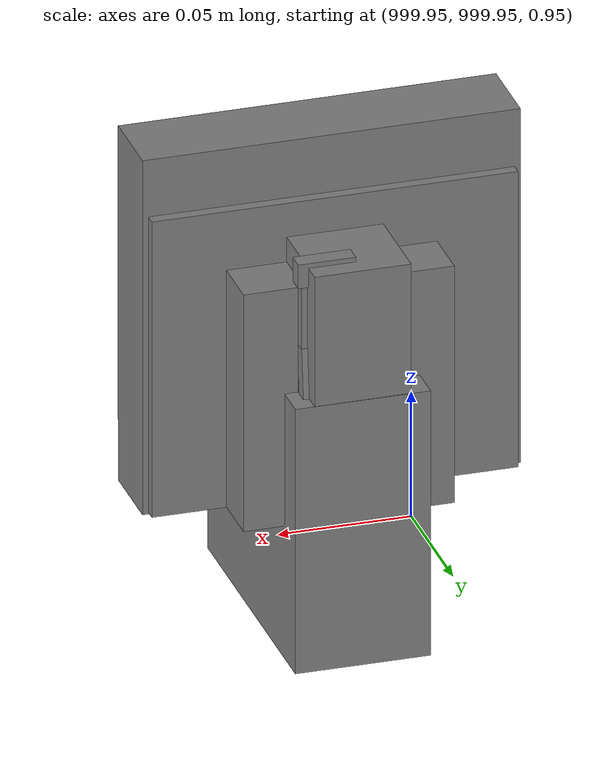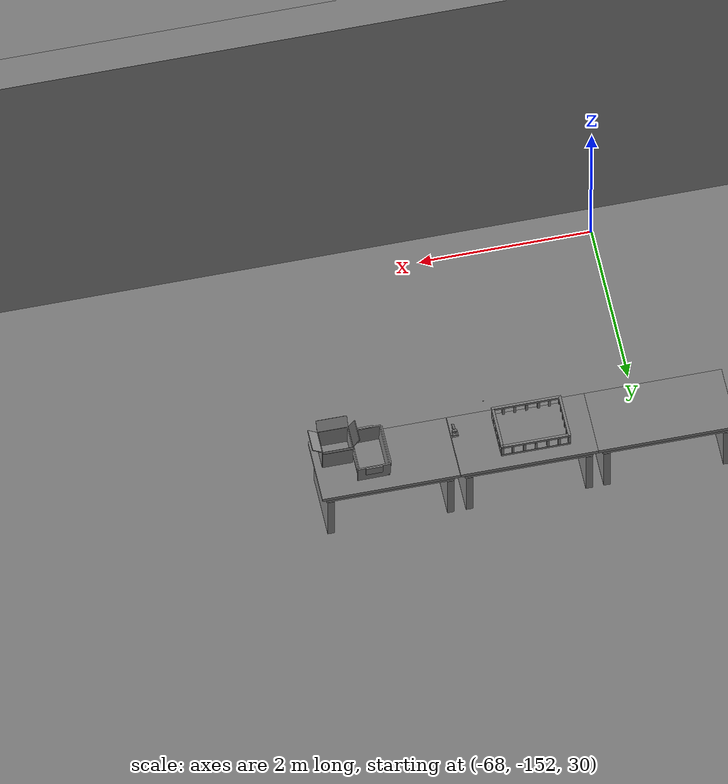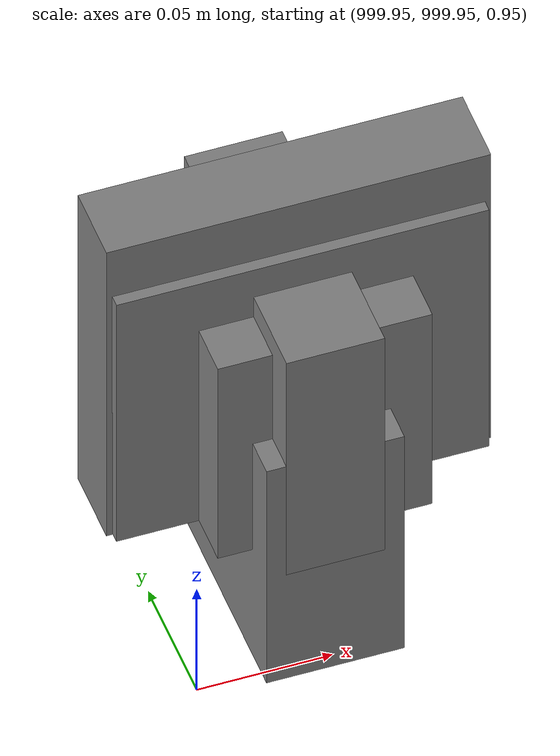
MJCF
<mujoco>
    <option gravity="0.000000000 0.000000000 -9.810000420" timestep="0.0049999999" integrator="implicitfast" density="1.225" viscosity="1.8000001e-05" noslip_iterations="10" iterations="100" sdf_iterations="50">
        <flag multiccd="disable"/>
    </option>
    <size memory="1000M"/>
    <compiler coordinate="local"/>
    <worldbody>
        <light cutoff="30" pos="0 1 1" dir="0 -1 -2"/>
        <light cutoff="30" pos="0 -1 1" dir="0 1 -2"/>
        <body pos="-64.866622925 -149.383972168 30.183746338" euler="89.999984741 89.999946594 0.000000000" name="openloong_gripper_2f85_fix_base_usda_bluebox_01">
            <geom contype="1" conaffinity="1" density="1000" type="box" material="" rgba="0.500000000 0.500000000 0.500000000 1.000000000" solimp="0.899999976 0.949999988 0.001000000" friction="1.000000000 0.005000000 0.000100000" solref="0.020000000 1.000000000" margin="0" condim="3" group="0" pos="0.276580811 0.187225342 0.000068665" quat="0.707106948 0.000077471 0.707106352 0.000077486" size="0.100000001 0.057999998 0.010000000" name="openloong_gripper_2f85_fix_base_usda_geom_B3007720_2E61_43AB_8FE3_21F2FBBA76D2"/>
            <geom contype="1" conaffinity="1" density="1000" type="box" material="" rgba="0.500000000 0.500000000 0.500000000 1.000000000" solimp="0.899999976 0.949999988 0.001000000" friction="1.000000000 0.005000000 0.000100000" solref="0.020000000 1.000000000" margin="0" condim="3" group="0" pos="0.000000000 0.002883911 0.000000000" quat="0.999999881 0.000000000 0.000000000 0.000000000" size="0.254000008 0.003000000 0.172000006" name="openloong_gripper_2f85_fix_base_usda_geom_C4C9F700_7050_4EBB_8D7E_EAC05A6D48B7"/>
            <geom contype="1" conaffinity="1" density="1000" type="box" material="" rgba="0.500000000 0.500000000 0.500000000 1.000000000" solimp="0.899999976 0.949999988 0.001000000" friction="1.000000000 0.005000000 0.000100000" solref="0.020000000 1.000000000" margin="0" condim="3" group="0" pos="0.000000000 0.124874115 0.173484802" quat="0.999796331 0.020176515 -0.000000015 0.000000030" size="0.259999990 0.119999997 0.007000000" name="openloong_gripper_2f85_fix_base_usda_geom_624E36EA_6404_481B_8E3E_E0E8FBBAD399"/>
            <geom contype="1" conaffinity="1" density="1000" type="box" material="" rgba="0.500000000 0.500000000 0.500000000 1.000000000" solimp="0.899999976 0.949999988 0.001000000" friction="1.000000000 0.005000000 0.000100000" solref="0.020000000 1.000000000" margin="0" condim="3" group="0" pos="0.000000000 0.124874115 -0.173469543" quat="0.999796331 -0.020176545 -0.000000015 0.000000000" size="0.259999990 0.119999997 0.007000000" name="openloong_gripper_2f85_fix_base_usda_geom_3AB7B79D_F4AE_4A39_9032_126DC0379528"/>
            <geom contype="1" conaffinity="1" density="1000" type="box" material="" rgba="0.500000000 0.500000000 0.500000000 1.000000000" solimp="0.899999976 0.949999988 0.001000000" friction="1.000000000 0.005000000 0.000100000" solref="0.020000000 1.000000000" margin="0" condim="3" group="0" pos="0.000000000 0.214008331 0.188980103" quat="0.999912977 0.013176724 0.000000015 0.000000000" size="0.259999990 0.029999999 0.012500000" name="openloong_gripper_2f85_fix_base_usda_geom_97610C33_266E_4FAB_9BF5_115491FFF3D8"/>
            <geom contype="1" conaffinity="1" density="1000" type="box" material="" rgba="0.500000000 0.500000000 0.500000000 1.000000000" solimp="0.899999976 0.949999988 0.001000000" friction="1.000000000 0.005000000 0.000100000" solref="0.020000000 1.000000000" margin="0" condim="3" group="0" pos="-0.258361816 0.125289917 0.001876831" quat="0.702796936 -0.020792112 0.710783124 0.020769298" size="0.189999998 0.119999997 0.009000000" name="openloong_gripper_2f85_fix_base_usda_geom_CD3CED04_5D13_47B0_8471_58C0661DBD7F"/>
            <geom contype="1" conaffinity="1" density="1000" type="box" material="" rgba="0.500000000 0.500000000 0.500000000 1.000000000" solimp="0.899999976 0.949999988 0.001000000" friction="1.000000000 0.005000000 0.000100000" solref="0.020000000 1.000000000" margin="0" condim="3" group="0" pos="0.000000000 0.214008331 -0.188980103" quat="0.999912977 -0.013176769 0.000000030 0.000000015" size="0.259999990 0.029999999 0.012500000" name="openloong_gripper_2f85_fix_base_usda_geom_84B7B404_2034_49D6_8746_34717D6E32A9"/>
            <geom contype="1" conaffinity="1" density="1000" type="box" material="" rgba="0.500000000 0.500000000 0.500000000 1.000000000" solimp="0.899999976 0.949999988 0.001000000" friction="1.000000000 0.005000000 0.000100000" solref="0.020000000 1.000000000" margin="0" condim="3" group="0" pos="-0.276611328 0.187225342 0.000068665" quat="0.707106650 0.000077441 0.707106709 0.000077456" size="0.100000001 0.057999998 0.010000000" name="openloong_gripper_2f85_fix_base_usda_geom_A2C8D677_BD19_4EA3_996E_51B9F1E88D64"/>
            <geom contype="1" conaffinity="1" density="1000" type="box" material="" rgba="0.500000000 0.500000000 0.500000000 1.000000000" solimp="0.899999976 0.949999988 0.001000000" friction="1.000000000 0.005000000 0.000100000" solref="0.020000000 1.000000000" margin="0" condim="3" group="0" pos="0.258331299 0.125289917 0.001876831" quat="0.702851415 0.018856421 0.710823774 -0.019329369" size="0.189999998 0.119999997 0.009000000" name="openloong_gripper_2f85_fix_base_usda_geom_4705D048_3518_43C9_AB7B_45910015C15B"/>
            <freejoint name="openloong_gripper_2f85_fix_base_usda_bluebox_01_joint"/>
            <site size="0.005000000 0.005000000 0.005000000" rgba="0.500000000 0.500000000 0.500000000 1.000000000" pos="0.000000000 0.000000000 0.000000000" quat="0.999961913 0.008726534 0.000000000 0.000000000" group="0" type="sphere" name="openloong_gripper_2f85_fix_base_usda_bluebox_01site"/>
        </body>
        <body pos="-64.496299744 -149.491867065 30.235729218" euler="0.000000000 0.000000000 89.999946594" name="openloong_gripper_2f85_fix_base_usda_cardboardbox_01">
            <geom contype="1" conaffinity="1" density="1000" type="box" material="" rgba="0.500000000 0.500000000 0.500000000 1.000000000" solimp="0.899999976 0.949999988 0.001000000" friction="1.000000000 0.005000000 0.000100000" solref="0.020000000 1.000000000" margin="0" condim="3" group="0" pos="-0.003166199 -0.004086494 0.005052090" quat="1.000000000 0.000000000 0.000000000 0.000000000" size="0.142499998 0.177500010 0.005000000" name="openloong_gripper_2f85_fix_base_usda_geom_473ABE09_17C8_408D_B8E1_EC1C0B5FE3E7"/>
            <geom contype="1" conaffinity="1" density="1000" type="box" material="" rgba="0.500000000 0.500000000 0.500000000 1.000000000" solimp="0.899999976 0.949999988 0.001000000" friction="1.000000000 0.005000000 0.000100000" solref="0.020000000 1.000000000" margin="0" condim="3" group="0" pos="-0.003166199 0.170316696 0.150570869" quat="1.000000000 0.000000000 0.000000000 0.000000000" size="0.142499998 0.005000000 0.149999991" name="openloong_gripper_2f85_fix_base_usda_geom_BAF6708F_B7B8_462E_8136_6E4B65D7B544"/>
            <geom contype="1" conaffinity="1" density="1000" type="box" material="" rgba="0.500000000 0.500000000 0.500000000 1.000000000" solimp="0.899999976 0.949999988 0.001000000" friction="1.000000000 0.005000000 0.000100000" solref="0.020000000 1.000000000" margin="0" condim="3" group="0" pos="-0.147399902 -0.005307198 0.150570869" quat="1.000000000 0.000000000 0.000000000 0.000000000" size="0.005000000 0.177500010 0.149999991" name="openloong_gripper_2f85_fix_base_usda_geom_A5D2E7BE_FC50_46FF_9A77_39B1019E0B54"/>
            <geom contype="1" conaffinity="1" density="1000" type="box" material="" rgba="0.500000000 0.500000000 0.500000000 1.000000000" solimp="0.899999976 0.949999988 0.001000000" friction="1.000000000 0.005000000 0.000100000" solref="0.020000000 1.000000000" margin="0" condim="3" group="0" pos="0.140275955 -0.005307198 0.150570869" quat="1.000000000 0.000000000 0.000000000 0.000000000" size="0.005000000 0.177500010 0.149999991" name="openloong_gripper_2f85_fix_base_usda_geom_ED9239B6_6DD2_4183_AD18_63B130121A39"/>
            <geom contype="1" conaffinity="1" density="1000" type="box" material="" rgba="0.500000000 0.500000000 0.500000000 1.000000000" solimp="0.899999976 0.949999988 0.001000000" friction="1.000000000 0.005000000 0.000100000" solref="0.020000000 1.000000000" margin="0" condim="3" group="0" pos="-0.003166199 -0.181550980 0.150570869" quat="1.000000000 0.000000000 0.000000000 0.000000000" size="0.142499998 0.005000000 0.149999991" name="openloong_gripper_2f85_fix_base_usda_geom_2EFD8731_17EC_44C5_A096_33D74D3F7788"/>
            <freejoint name="openloong_gripper_2f85_fix_base_usda_cardboardbox_01_joint"/>
            <site size="0.005000000 0.005000000 0.005000000" rgba="0.500000000 0.500000000 0.500000000 1.000000000" pos="0.000000000 0.000000000 0.000000000" quat="0.999961913 0.008726535 0.000000000 0.000000000" group="0" type="sphere" name="openloong_gripper_2f85_fix_base_usda_site_C961D0AC_1CDD_477F_9CC9_C8C80E2AF68A"/>
            <body pos="0.139160156 -0.004048347 0.301930904" euler="-179.999954224 49.383502960 179.999954224" name="openloong_gripper_2f85_fix_base_usda_A1_006">
                <geom contype="1" conaffinity="1" density="1000" type="box" material="" rgba="0.500000000 0.500000000 0.500000000 1.000000000" solimp="0.899999976 0.949999988 0.001000000" friction="1.000000000 0.005000000 0.000100000" solref="0.020000000 1.000000000" margin="0" condim="3" group="0" pos="-0.071587563 0.000009537 0.001745224" quat="0.999999881 0.000000000 0.000000000 0.000000000" size="0.071249999 0.179999992 0.002500000" name="openloong_gripper_2f85_fix_base_usda_geom_79DBCCE7_A04C_4DF8_BF46_A73EF50B2856"/>
                <joint armature="0" stiffness="0.07" damping="0.0099999998" axis="0.000000 1.000000 0.000000" type="hinge" name="openloong_gripper_2f85_fix_base_usda_A1_006"/>
            </body>
            <body pos="-0.145902634 -0.004086494 0.301938057" euler="-180.000000000 -60.000011444 -180.000000000" name="openloong_gripper_2f85_fix_base_usda_A2_006">
                <geom contype="1" conaffinity="1" density="1000" type="box" material="" rgba="0.500000000 0.500000000 0.500000000 1.000000000" solimp="0.899999976 0.949999988 0.001000000" friction="1.000000000 0.005000000 0.000100000" solref="0.020000000 1.000000000" margin="0" condim="3" group="0" pos="0.071268082 0.000009537 0.002717972" quat="0.000002921 0.000000000 -0.000000030 0.999999881" size="0.071249999 0.179999992 0.002500000" name="openloong_gripper_2f85_fix_base_usda_geom_3133CD88_24FC_423D_9949_E21B97352729"/>
                <joint armature="0" stiffness="0.07" damping="0.0099999998" axis="0.000000 1.000000 0.000000" type="hinge" name="openloong_gripper_2f85_fix_base_usda_A2_006"/>
            </body>
            <body pos="-0.003385544 0.175991058 0.301930904" euler="-125.858116150 -0.000004561 0.000002331" name="openloong_gripper_2f85_fix_base_usda_B2_006">
                <geom contype="1" conaffinity="1" density="1000" type="box" material="" rgba="0.500000000 0.500000000 0.500000000 1.000000000" solimp="0.899999976 0.949999988 0.001000000" friction="1.000000000 0.005000000 0.000100000" solref="0.020000000 1.000000000" margin="0" condim="3" group="0" pos="0.000009537 -0.070939064 -0.002470016" quat="0.999614120 0.027776197 -0.000000015 0.000000030" size="0.137500003 0.064999998 0.005000000" name="openloong_gripper_2f85_fix_base_usda_geom_01EB228F_12AD_4B4A_9CA2_4AB63B271430"/>
                <joint armature="0" stiffness="0.07" damping="0.0099999998" axis="1.000000 0.000000 0.000000" type="hinge" name="openloong_gripper_2f85_fix_base_usda_B2_006"/>
            </body>
            <body pos="-0.003385544 -0.184140205 0.301938057" euler="147.805557251 0.000000000 0.000000000" name="openloong_gripper_2f85_fix_base_usda_B1_006">
                <geom contype="1" conaffinity="1" density="1000" type="box" material="" rgba="0.500000000 0.500000000 0.500000000 1.000000000" solimp="0.899999976 0.949999988 0.001000000" friction="1.000000000 0.005000000 0.000100000" solref="0.020000000 1.000000000" margin="0" condim="3" group="0" pos="-0.000028610 0.070202351 -0.002703667" quat="0.999614179 -0.027776167 0.000000000 0.000000000" size="0.137500003 0.064999998 0.005000000" name="openloong_gripper_2f85_fix_base_usda_geom_D7CD3A9D_C371_4C17_AD30_B913D60C398D"/>
                <joint armature="0" stiffness="0.07" damping="0.0099999998" axis="1.000000 0.000000 0.000000" type="hinge" name="openloong_gripper_2f85_fix_base_usda_B1_006"/>
            </body>
        </body>
        <body pos="-65.882858276 -149.481979370 30.229999542" euler="-64.487716675 0.000000000 0.000000000" name="openloong_gripper_2f85_fix_base_usda_Barcode">
            <geom contype="1" conaffinity="1" density="1000" type="box" material="" rgba="0.500000000 0.500000000 0.500000000 1.000000000" solimp="0.899999976 0.949999988 0.001000000" friction="1.000000000 0.005000000 0.000100000" solref="0.020000000 1.000000000" margin="0" condim="3" group="0" pos="0.000000000 0.013038635 0.001419067" quat="0.000000000 0.000000000 0.000000000 1.000000119" size="0.034000002 0.010000000 0.017999999" name="openloong_gripper_2f85_fix_base_usda_geom_0A1D2402_6001_4513_AF97_C284BB0CDCBA"/>
            <geom contype="1" conaffinity="1" density="1000" type="box" material="" rgba="0.500000000 0.500000000 0.500000000 1.000000000" solimp="0.899999976 0.949999988 0.001000000" friction="1.000000000 0.005000000 0.000100000" solref="0.020000000 1.000000000" margin="0" condim="3" group="0" pos="0.000000000 -0.035301208 -0.007095337" quat="0.000000000 0.000000000 -0.043619365 0.999048233" size="0.028999999 0.010000000 0.020000000" name="openloong_gripper_2f85_fix_base_usda_geom_DDD93CF2_89DC_44A7_A33F_40FABBE75B9E"/>
            <geom contype="1" conaffinity="1" density="1000" type="box" material="" rgba="0.500000000 0.500000000 0.500000000 1.000000000" solimp="0.899999976 0.949999988 0.001000000" friction="1.000000000 0.005000000 0.000100000" solref="0.020000000 1.000000000" margin="0" condim="3" group="0" pos="0.000000000 -0.043411255 -0.011749268" quat="0.922262907 0.386563420 0.000000000 0.000000000" size="0.026000001 0.010000000 0.020000000" name="openloong_gripper_2f85_fix_base_usda_geom_6EBE708C_DFB0_44AD_835E_02BB83FECB23"/>
            <geom contype="1" conaffinity="1" density="1000" type="box" material="" rgba="0.500000000 0.500000000 0.500000000 1.000000000" solimp="0.899999976 0.949999988 0.001000000" friction="1.000000000 0.005000000 0.000100000" solref="0.020000000 1.000000000" margin="0" condim="3" group="0" pos="0.000000000 -0.016967773 -0.031860352" quat="0.000000000 0.000000000 0.000000000 1.000000119" size="0.008000000 0.010000000 0.013000000" name="openloong_gripper_2f85_fix_base_usda_geom_66AFD90C_340A_4AD2_8576_6A67FD2E8043"/>
            <geom contype="1" conaffinity="1" density="1000" type="box" material="" rgba="0.500000000 0.500000000 0.500000000 1.000000000" solimp="0.899999976 0.949999988 0.001000000" friction="1.000000000 0.005000000 0.000100000" solref="0.020000000 1.000000000" margin="0" condim="3" group="0" pos="0.000000000 -0.001869202 0.000312805" quat="0.953716993 0.300705761 0.000000000 0.000000000" size="0.032000002 0.010000000 0.018999999" name="openloong_gripper_2f85_fix_base_usda_geom_4FDBBEB7_D61C_4B4F_80A3_A2A3B24D10A0"/>
            <geom contype="1" conaffinity="1" density="1000" type="box" material="" rgba="0.500000000 0.500000000 0.500000000 1.000000000" solimp="0.899999976 0.949999988 0.001000000" friction="1.000000000 0.005000000 0.000100000" solref="0.020000000 1.000000000" margin="0" condim="3" group="0" pos="0.000000000 -0.019531250 -0.003173828" quat="0.953716993 0.300705761 0.000000000 0.000000000" size="0.030999999 0.010000000 0.020000000" name="openloong_gripper_2f85_fix_base_usda_geom_B1284CF2_62C9_4AC8_BB00_F599EBC4AA20"/>
            <geom contype="1" conaffinity="1" density="1000" type="box" material="" rgba="0.500000000 0.500000000 0.500000000 1.000000000" solimp="0.899999976 0.949999988 0.001000000" friction="1.000000000 0.005000000 0.000100000" solref="0.020000000 1.000000000" margin="0" condim="3" group="0" pos="0.000000000 -0.035301208 -0.007095337" quat="0.953716993 0.300705761 0.000000000 0.000000000" size="0.028999999 0.010000000 0.020000000" name="openloong_gripper_2f85_fix_base_usda_geom_B01160B9_14C9_491F_8D52_31DFD6801C11"/>
            <geom contype="1" conaffinity="1" density="1000" type="box" material="" rgba="0.500000000 0.500000000 0.500000000 1.000000000" solimp="0.899999976 0.949999988 0.001000000" friction="1.000000000 0.005000000 0.000100000" solref="0.020000000 1.000000000" margin="0" condim="3" group="0" pos="0.000000000 -0.042617798 -0.071121216" quat="0.000000000 0.000000000 0.000000000 1.000000119" size="0.013000000 0.021000000 0.059999999" name="openloong_gripper_2f85_fix_base_usda_geom_25F6A7BC_AE73_4327_AB5D_300709DF0D74"/>
            <freejoint name="openloong_gripper_2f85_fix_base_usda_Barcode_joint"/>
            <site size="0.005000000 0.005000000 0.005000000" rgba="0.500000000 0.500000000 0.500000000 1.000000000" pos="0.000000000 0.000000000 0.000000000" quat="1.000000000 0.000000000 0.000000000 0.000000000" group="0" type="sphere" name="openloong_gripper_2f85_fix_base_usda_Barcode_site"/>
        </body>
        <body pos="-66.745018005 -149.392349243 30.184000015" euler="0.000000000 0.000000000 89.999946594" name="[22333274631718]_Basket_01">
            <geom contype="1" conaffinity="1" density="1000" type="box" material="" rgba="0.500000000 0.500000000 0.500000000 1.000000000" solimp="0.899999976 0.949999988 0.001000000" friction="1.000000000 0.005000000 0.000100000" solref="0.020000000 1.000000000" margin="0" condim="3" group="0" pos="-0.052425385 0.389207840 0.089787483" quat="0.707107008 0.000000000 0.000000000 0.707106411" size="0.014249999 0.014249999 0.059999999" name="[22333274631718]_geom_79BF8442_A6A2_498E_95EB_F7A10DF4BF2D"/>
            <geom contype="1" conaffinity="1" density="1000" type="box" material="" rgba="0.500000000 0.500000000 0.500000000 1.000000000" solimp="0.899999976 0.949999988 0.001000000" friction="1.000000000 0.005000000 0.000100000" solref="0.020000000 1.000000000" margin="0" condim="3" group="0" pos="0.264015198 -0.133043289 0.089787483" quat="0.707107008 0.000000000 0.000000000 0.707106411" size="0.014249999 0.014249999 0.059999999" name="[22333274631718]_geom_B5EF4F2B_7B14_432F_927C_D4EFD62C7985"/>
            <geom contype="1" conaffinity="1" density="1000" type="box" material="" rgba="0.500000000 0.500000000 0.500000000 1.000000000" solimp="0.899999976 0.949999988 0.001000000" friction="1.000000000 0.005000000 0.000100000" solref="0.020000000 1.000000000" margin="0" condim="3" group="0" pos="-0.264015198 -0.265548706 0.089793205" quat="0.707107008 0.000000000 0.000000000 0.707106411" size="0.014249999 0.014249999 0.059999999" name="[22333274631718]_geom_39354E8E_7F1C_4C0B_8AE3_1896DBCAC544"/>
            <geom contype="1" conaffinity="1" density="1000" type="box" material="" rgba="0.500000000 0.500000000 0.500000000 1.000000000" solimp="0.899999976 0.949999988 0.001000000" friction="1.000000000 0.005000000 0.000100000" solref="0.020000000 1.000000000" margin="0" condim="3" group="0" pos="-0.160263062 -0.389322281 0.089793205" quat="0.707107008 0.000000000 0.000000000 0.707106411" size="0.014249999 0.014249999 0.059999999" name="[22333274631718]_geom_059E994C_E774_4F4F_87FC_234DE46ABFFA"/>
            <geom contype="1" conaffinity="1" density="1000" type="box" material="" rgba="0.500000000 0.500000000 0.500000000 1.000000000" solimp="0.899999976 0.949999988 0.001000000" friction="1.000000000 0.005000000 0.000100000" solref="0.020000000 1.000000000" margin="0" condim="3" group="0" pos="0.162265778 -0.389322281 0.089787483" quat="0.707107008 0.000000000 0.000000000 0.707106411" size="0.014249999 0.014249999 0.059999999" name="[22333274631718]_geom_C5CE005E_77B5_4C41_8337_5DED79146815"/>
            <geom contype="1" conaffinity="1" density="1000" type="box" material="" rgba="0.500000000 0.500000000 0.500000000 1.000000000" solimp="0.899999976 0.949999988 0.001000000" friction="1.000000000 0.005000000 0.000100000" solref="0.020000000 1.000000000" margin="0" condim="3" group="0" pos="0.264015198 0.389207840 0.089787483" quat="0.707107008 0.000000000 0.000000000 0.707106411" size="0.014249999 0.014249999 0.059999999" name="[22333274631718]_geom_58E1C43F_BE8D_4770_A196_E9BB4A01F16B"/>
            <geom contype="1" conaffinity="1" density="1000" type="box" material="" rgba="0.500000000 0.500000000 0.500000000 1.000000000" solimp="0.899999976 0.949999988 0.001000000" friction="1.000000000 0.005000000 0.000100000" solref="0.020000000 1.000000000" margin="0" condim="3" group="0" pos="-0.264015198 -0.133043289 0.089793205" quat="0.707107008 0.000000000 0.000000000 0.707106411" size="0.014249999 0.014249999 0.059999999" name="[22333274631718]_geom_76C8A984_317C_4306_80EA_BC90D5AD9E9E"/>
            <geom contype="1" conaffinity="1" density="1000" type="box" material="" rgba="0.500000000 0.500000000 0.500000000 1.000000000" solimp="0.899999976 0.949999988 0.001000000" friction="1.000000000 0.005000000 0.000100000" solref="0.020000000 1.000000000" margin="0" condim="3" group="0" pos="-0.264026642 0.269256592 0.089793205" quat="0.707107008 0.000000000 0.000000000 0.707106411" size="0.014249999 0.014249999 0.059999999" name="[22333274631718]_geom_43EDA4C3_E21B_4F26_BA65_A36302CE2A5B"/>
            <geom contype="1" conaffinity="1" density="1000" type="box" material="" rgba="0.500000000 0.500000000 0.500000000 1.000000000" solimp="0.899999976 0.949999988 0.001000000" friction="1.000000000 0.005000000 0.000100000" solref="0.020000000 1.000000000" margin="0" condim="3" group="0" pos="0.054462433 0.389207840 0.089787483" quat="0.707107008 0.000000000 0.000000000 0.707106411" size="0.014249999 0.014249999 0.059999999" name="[22333274631718]_geom_BB97DF3E_FA57_458D_8707_A8E62B4D52DB"/>
            <geom contype="1" conaffinity="1" density="1000" type="box" material="" rgba="0.500000000 0.500000000 0.500000000 1.000000000" solimp="0.899999976 0.949999988 0.001000000" friction="1.000000000 0.005000000 0.000100000" solref="0.020000000 1.000000000" margin="0" condim="3" group="0" pos="0.054462433 -0.389322281 0.089787483" quat="0.707107008 0.000000000 0.000000000 0.707106411" size="0.014249999 0.014249999 0.059999999" name="[22333274631718]_geom_252E6EC9_6C97_475D_BD8B_6F0292813923"/>
            <geom contype="1" conaffinity="1" density="1000" type="box" material="" rgba="0.500000000 0.500000000 0.500000000 1.000000000" solimp="0.899999976 0.949999988 0.001000000" friction="1.000000000 0.005000000 0.000100000" solref="0.020000000 1.000000000" margin="0" condim="3" group="0" pos="0.264015198 0.269256592 0.089793205" quat="0.707107008 0.000000000 0.000000000 0.707106411" size="0.014249999 0.014249999 0.059999999" name="[22333274631718]_geom_9B17E754_9648_4EC2_A95E_C5A9076E0FE6"/>
            <geom contype="1" conaffinity="1" density="1000" type="box" material="" rgba="0.500000000 0.500000000 0.500000000 1.000000000" solimp="0.899999976 0.949999988 0.001000000" friction="1.000000000 0.005000000 0.000100000" solref="0.020000000 1.000000000" margin="0" condim="3" group="0" pos="0.264015198 -0.389322281 0.089787483" quat="0.707107008 0.000000000 0.000000000 0.707106411" size="0.014249999 0.014249999 0.059999999" name="[22333274631718]_geom_FF1F41F8_5F49_4A12_9D2B_3FAA6FAB19EA"/>
            <geom contype="1" conaffinity="1" density="1000" type="box" material="" rgba="0.500000000 0.500000000 0.500000000 1.000000000" solimp="0.899999976 0.949999988 0.001000000" friction="1.000000000 0.005000000 0.000100000" solref="0.020000000 1.000000000" margin="0" condim="3" group="0" pos="0.000000000 0.000000000 0.015998840" quat="0.707107008 0.000000000 0.000000000 0.707106411" size="0.403499991 0.279000014 0.015750000" name="[22333274631718]_geom_30345616_8247_48F6_93D2_977195E2018B"/>
            <geom contype="1" conaffinity="1" density="1000" type="box" material="" rgba="0.500000000 0.500000000 0.500000000 1.000000000" solimp="0.899999976 0.949999988 0.001000000" friction="1.000000000 0.005000000 0.000100000" solref="0.020000000 1.000000000" margin="0" condim="3" group="0" pos="0.000000000 -0.389476776 0.163619041" quat="0.707107008 0.000000000 0.000000000 0.707106411" size="0.015000000 0.277500004 0.015750000" name="[22333274631718]_geom_06D3E071_0697_4189_9153_7FCB285E6318"/>
            <geom contype="1" conaffinity="1" density="1000" type="box" material="" rgba="0.500000000 0.500000000 0.500000000 1.000000000" solimp="0.899999976 0.949999988 0.001000000" friction="1.000000000 0.005000000 0.000100000" solref="0.020000000 1.000000000" margin="0" condim="3" group="0" pos="0.162265778 0.389207840 0.089787483" quat="0.707107008 0.000000000 0.000000000 0.707106411" size="0.014249999 0.014249999 0.059999999" name="[22333274631718]_geom_52C4250B_A2FA_42FF_917A_117CF3E93318"/>
            <geom contype="1" conaffinity="1" density="1000" type="box" material="" rgba="0.500000000 0.500000000 0.500000000 1.000000000" solimp="0.899999976 0.949999988 0.001000000" friction="1.000000000 0.005000000 0.000100000" solref="0.020000000 1.000000000" margin="0" condim="3" group="0" pos="0.000000000 0.389471054 0.163619041" quat="0.707107008 0.000000000 0.000000000 0.707106411" size="0.015000000 0.277500004 0.015750000" name="[22333274631718]_geom_DC4537B4_FB41_4DA1_8658_873D42598335"/>
            <geom contype="1" conaffinity="1" density="1000" type="box" material="" rgba="0.500000000 0.500000000 0.500000000 1.000000000" solimp="0.899999976 0.949999988 0.001000000" friction="1.000000000 0.005000000 0.000100000" solref="0.020000000 1.000000000" margin="0" condim="3" group="0" pos="-0.263511658 0.000000000 0.163619041" quat="0.707107008 0.000000000 0.000000000 0.707106411" size="0.403499991 0.015000000 0.015750000" name="[22333274631718]_geom_DDCDAD74_9A0F_4F20_BE64_C4A1F370FE93"/>
            <geom contype="1" conaffinity="1" density="1000" type="box" material="" rgba="0.500000000 0.500000000 0.500000000 1.000000000" solimp="0.899999976 0.949999988 0.001000000" friction="1.000000000 0.005000000 0.000100000" solref="0.020000000 1.000000000" margin="0" condim="3" group="0" pos="-0.264015198 0.141334534 0.089793205" quat="0.707107008 0.000000000 0.000000000 0.707106411" size="0.014249999 0.014249999 0.059999999" name="[22333274631718]_geom_27364C76_32A1_4861_AFFF_D4BC3CEC5639"/>
            <geom contype="1" conaffinity="1" density="1000" type="box" material="" rgba="0.500000000 0.500000000 0.500000000 1.000000000" solimp="0.899999976 0.949999988 0.001000000" friction="1.000000000 0.005000000 0.000100000" solref="0.020000000 1.000000000" margin="0" condim="3" group="0" pos="0.264015198 -0.265548706 0.089787483" quat="0.707107008 0.000000000 0.000000000 0.707106411" size="0.014249999 0.014249999 0.059999999" name="[22333274631718]_geom_DA7D002D_9A4A_4596_AB4E_E8213AF5237A"/>
            <geom contype="1" conaffinity="1" density="1000" type="box" material="" rgba="0.500000000 0.500000000 0.500000000 1.000000000" solimp="0.899999976 0.949999988 0.001000000" friction="1.000000000 0.005000000 0.000100000" solref="0.020000000 1.000000000" margin="0" condim="3" group="0" pos="-0.160263062 0.389207840 0.089787483" quat="0.707107008 0.000000000 0.000000000 0.707106411" size="0.014249999 0.014249999 0.059999999" name="[22333274631718]_geom_53A4BD23_2847_434A_AD0B_9C8C104627F8"/>
            <geom contype="1" conaffinity="1" density="1000" type="box" material="" rgba="0.500000000 0.500000000 0.500000000 1.000000000" solimp="0.899999976 0.949999988 0.001000000" friction="1.000000000 0.005000000 0.000100000" solref="0.020000000 1.000000000" margin="0" condim="3" group="0" pos="-0.052425385 -0.389322281 0.089787483" quat="0.707107008 0.000000000 0.000000000 0.707106411" size="0.014249999 0.014249999 0.059999999" name="[22333274631718]_geom_4CE56089_2FF8_47C9_A456_757DC56E68FF"/>
            <geom contype="1" conaffinity="1" density="1000" type="box" material="" rgba="0.500000000 0.500000000 0.500000000 1.000000000" solimp="0.899999976 0.949999988 0.001000000" friction="1.000000000 0.005000000 0.000100000" solref="0.020000000 1.000000000" margin="0" condim="3" group="0" pos="-0.264026642 -0.389322281 0.089793205" quat="0.707107008 0.000000000 0.000000000 0.707106411" size="0.014249999 0.014249999 0.059999999" name="[22333274631718]_geom_D59A44AA_4F57_42D8_963D_107788042EF3"/>
            <geom contype="1" conaffinity="1" density="1000" type="box" material="" rgba="0.500000000 0.500000000 0.500000000 1.000000000" solimp="0.899999976 0.949999988 0.001000000" friction="1.000000000 0.005000000 0.000100000" solref="0.020000000 1.000000000" margin="0" condim="3" group="0" pos="0.264015198 0.141334534 0.089787483" quat="0.707107008 0.000000000 0.000000000 0.707106411" size="0.014249999 0.014249999 0.059999999" name="[22333274631718]_geom_4059A3CD_2A89_4AC4_960D_282D649A559F"/>
            <geom contype="1" conaffinity="1" density="1000" type="box" material="" rgba="0.500000000 0.500000000 0.500000000 1.000000000" solimp="0.899999976 0.949999988 0.001000000" friction="1.000000000 0.005000000 0.000100000" solref="0.020000000 1.000000000" margin="0" condim="3" group="0" pos="-0.264015198 0.389207840 0.089793205" quat="0.707107008 0.000000000 0.000000000 0.707106411" size="0.014249999 0.014249999 0.059999999" name="[22333274631718]_geom_E737690B_1D60_4A97_9CD4_8DC6ABBEE7AA"/>
            <geom contype="1" conaffinity="1" density="1000" type="box" material="" rgba="0.500000000 0.500000000 0.500000000 1.000000000" solimp="0.899999976 0.949999988 0.001000000" friction="1.000000000 0.005000000 0.000100000" solref="0.020000000 1.000000000" margin="0" condim="3" group="0" pos="0.264015198 0.004480362 0.089787483" quat="0.707107008 0.000000000 0.000000000 0.707106411" size="0.014249999 0.014249999 0.059999999" name="[22333274631718]_geom_35CBA7E2_7342_43CB_AF33_A7F7553CFFA9"/>
            <geom contype="1" conaffinity="1" density="1000" type="box" material="" rgba="0.500000000 0.500000000 0.500000000 1.000000000" solimp="0.899999976 0.949999988 0.001000000" friction="1.000000000 0.005000000 0.000100000" solref="0.020000000 1.000000000" margin="0" condim="3" group="0" pos="0.263694763 -0.000011444 0.163619041" quat="0.707107008 0.000000000 0.000000000 0.707106411" size="0.403499991 0.015000000 0.015750000" name="[22333274631718]_geom_5F4584D6_C9B3_489E_B749_6627430D08FC"/>
            <geom contype="1" conaffinity="1" density="1000" type="box" material="" rgba="0.500000000 0.500000000 0.500000000 1.000000000" solimp="0.899999976 0.949999988 0.001000000" friction="1.000000000 0.005000000 0.000100000" solref="0.020000000 1.000000000" margin="0" condim="3" group="0" pos="-0.264015198 0.004480362 0.089793205" quat="0.707107008 0.000000000 0.000000000 0.707106411" size="0.014249999 0.014249999 0.059999999" name="[22333274631718]_geom_657AD772_3198_459B_BBF0_FD4586D42ECD"/>
            <freejoint name="[22333274631718]_joint_5B9CA4A9_4B7C_4332_A46A_7D61AFD8BE01"/>
        </body>
        <body pos="0.000000000 0.000000000 0.000000000" euler="0.000000000 0.000000000 0.000000000" name="Static Objects_Static Objects">
            <geom contype="1" conaffinity="1" density="1000" type="box" material="" rgba="0.500000000 0.500000000 0.500000000 1.000000000" solimp="0.899999976 0.949999988 0.001000000" friction="1.000000000 0.005000000 0.000100000" solref="0.020000000 1.000000000" margin="0" condim="3" group="0" pos="-67.544113159 -149.365814209 29.727830887" quat="0.500000417 0.499999970 0.499999553 0.499999970" size="0.381000012 0.319999993 0.041000001" name="Static Objects_geom_47A9796B_8099_47DC_ADC4_9ADA16EF88F1"/>
            <geom contype="1" conaffinity="1" density="1000" type="box" material="" rgba="0.500000000 0.500000000 0.500000000 1.000000000" solimp="0.899999976 0.949999988 0.001000000" friction="1.000000000 0.005000000 0.000100000" solref="0.020000000 1.000000000" margin="0" condim="3" group="0" pos="-68.239501953 -149.365814209 30.086868286" quat="0.500000417 0.499999970 0.499999553 0.499999970" size="0.370999992 0.039500002 0.745000005" name="Static Objects_geom_5A0768A4_5C92_45E8_AA31_46FD8A304F1F"/>
            <geom contype="1" conaffinity="1" density="1000" type="box" material="" rgba="0.500000000 0.500000000 0.500000000 1.000000000" solimp="0.899999976 0.949999988 0.001000000" friction="1.000000000 0.005000000 0.000100000" solref="0.020000000 1.000000000" margin="0" condim="3" group="0" pos="-68.239501953 -149.365814209 30.147235870" quat="0.500000417 0.499999970 0.499999553 0.499999970" size="0.400000006 0.022000000 0.800000012" name="Static Objects_geom_CD28B0D0_CF43_4EFC_89B2_3B04E7155B8E"/>
            <geom contype="1" conaffinity="1" density="1000" type="box" material="" rgba="0.500000000 0.500000000 0.500000000 1.000000000" solimp="0.899999976 0.949999988 0.001000000" friction="1.000000000 0.005000000 0.000100000" solref="0.020000000 1.000000000" margin="0" condim="3" group="0" pos="-68.934890747 -149.365814209 29.727830887" quat="0.500000417 0.499999970 0.499999553 0.499999970" size="0.381000012 0.319999993 0.041000001" name="Static Objects_geom_FEE89993_180C_40A5_A181_93377396EAB5"/>
            <geom contype="1" conaffinity="1" density="1000" type="box" material="" rgba="0.500000000 0.500000000 0.500000000 1.000000000" solimp="0.899999976 0.949999988 0.001000000" friction="1.000000000 0.005000000 0.000100000" solref="0.020000000 1.000000000" margin="0" condim="3" group="0" pos="-68.239501953 -149.365814209 29.561563492" quat="0.500000417 0.499999970 0.499999553 0.499999970" size="0.020000000 0.022000000 0.660000026" name="Static Objects_geom_CFDEBA3B_3DF9_467F_89F8_DD998751A6ED"/>
            <geom contype="1" conaffinity="1" density="1000" type="box" material="" rgba="0.500000000 0.500000000 0.500000000 1.000000000" solimp="0.899999976 0.949999988 0.001000000" friction="1.000000000 0.005000000 0.000100000" solref="0.020000000 1.000000000" margin="0" condim="3" group="0" pos="-65.945671082 -149.365814209 29.727830887" quat="0.500000417 0.499999970 0.499999553 0.499999970" size="0.381000012 0.319999993 0.041000001" name="Static Objects_geom_7165D2DB_DC1B_4458_95F1_2582B66F165B"/>
            <geom contype="1" conaffinity="1" density="1000" type="box" material="" rgba="0.500000000 0.500000000 0.500000000 1.000000000" solimp="0.899999976 0.949999988 0.001000000" friction="1.000000000 0.005000000 0.000100000" solref="0.020000000 1.000000000" margin="0" condim="3" group="0" pos="-66.641059875 -149.365814209 30.086868286" quat="0.500000417 0.499999970 0.499999553 0.499999970" size="0.370999992 0.039500002 0.745000005" name="Static Objects_geom_E1B52562_7185_4684_884A_1EFAD93D8F1D"/>
            <geom contype="1" conaffinity="1" density="1000" type="box" material="" rgba="0.500000000 0.500000000 0.500000000 1.000000000" solimp="0.899999976 0.949999988 0.001000000" friction="1.000000000 0.005000000 0.000100000" solref="0.020000000 1.000000000" margin="0" condim="3" group="0" pos="-66.641059875 -149.365814209 30.147235870" quat="0.500000417 0.499999970 0.499999553 0.499999970" size="0.400000006 0.022000000 0.800000012" name="Static Objects_geom_2D65825B_67F6_4088_B40D_2C73C804B87D"/>
            <geom contype="1" conaffinity="1" density="1000" type="box" material="" rgba="0.500000000 0.500000000 0.500000000 1.000000000" solimp="0.899999976 0.949999988 0.001000000" friction="1.000000000 0.005000000 0.000100000" solref="0.020000000 1.000000000" margin="0" condim="3" group="0" pos="-67.336448669 -149.365814209 29.727830887" quat="0.500000417 0.499999970 0.499999553 0.499999970" size="0.381000012 0.319999993 0.041000001" name="Static Objects_geom_BDEB6D82_D1E0_4F5C_80DC_895D72E2510B"/>
            <geom contype="1" conaffinity="1" density="1000" type="box" material="" rgba="0.500000000 0.500000000 0.500000000 1.000000000" solimp="0.899999976 0.949999988 0.001000000" friction="1.000000000 0.005000000 0.000100000" solref="0.020000000 1.000000000" margin="0" condim="3" group="0" pos="-66.641059875 -149.365814209 29.561563492" quat="0.500000417 0.499999970 0.499999553 0.499999970" size="0.020000000 0.022000000 0.660000026" name="Static Objects_geom_6A989843_748A_44B7_A108_9A121A10319C"/>
            <geom contype="1" conaffinity="1" density="1000" type="box" material="" rgba="0.500000000 0.500000000 0.500000000 1.000000000" solimp="0.899999976 0.949999988 0.001000000" friction="1.000000000 0.005000000 0.000100000" solref="0.020000000 1.000000000" margin="0" condim="3" group="0" pos="-64.338577271 -149.365814209 29.727830887" quat="0.500000417 0.499999970 0.499999553 0.499999970" size="0.381000012 0.319999993 0.041000001" name="Static Objects_geom_27D91D8F_FAE2_4C30_810D_2F005CE055FC"/>
            <geom contype="1" conaffinity="1" density="1000" type="box" material="" rgba="0.500000000 0.500000000 0.500000000 1.000000000" solimp="0.899999976 0.949999988 0.001000000" friction="1.000000000 0.005000000 0.000100000" solref="0.020000000 1.000000000" margin="0" condim="3" group="0" pos="-65.033966064 -149.365814209 30.086868286" quat="0.500000417 0.499999970 0.499999553 0.499999970" size="0.370999992 0.039500002 0.745000005" name="Static Objects_geom_738E5DA6_C387_4C85_A1B5_74498BCE5A7A"/>
            <geom contype="1" conaffinity="1" density="1000" type="box" material="" rgba="0.500000000 0.500000000 0.500000000 1.000000000" solimp="0.899999976 0.949999988 0.001000000" friction="1.000000000 0.005000000 0.000100000" solref="0.020000000 1.000000000" margin="0" condim="3" group="0" pos="-65.033966064 -149.365814209 30.147235870" quat="0.500000417 0.499999970 0.499999553 0.499999970" size="0.400000006 0.022000000 0.800000012" name="Static Objects_geom_2E7DDDDE_7A98_46A2_97AD_D0EE98A43C9E"/>
            <geom contype="1" conaffinity="1" density="1000" type="box" material="" rgba="0.500000000 0.500000000 0.500000000 1.000000000" solimp="0.899999976 0.949999988 0.001000000" friction="1.000000000 0.005000000 0.000100000" solref="0.020000000 1.000000000" margin="0" condim="3" group="0" pos="-65.729354858 -149.365814209 29.727830887" quat="0.500000417 0.499999970 0.499999553 0.499999970" size="0.381000012 0.319999993 0.041000001" name="Static Objects_geom_02CB85A9_4D25_4C8A_8DCC_258764E3D89F"/>
            <geom contype="1" conaffinity="1" density="1000" type="box" material="" rgba="0.500000000 0.500000000 0.500000000 1.000000000" solimp="0.899999976 0.949999988 0.001000000" friction="1.000000000 0.005000000 0.000100000" solref="0.020000000 1.000000000" margin="0" condim="3" group="0" pos="-65.033966064 -149.365814209 29.561563492" quat="0.500000417 0.499999970 0.499999553 0.499999970" size="0.020000000 0.022000000 0.660000026" name="Static Objects_geom_5889A0E7_B273_489C_8196_A2AD30A76873"/>
            <geom contype="1" conaffinity="1" density="1000" type="box" material="" rgba="0.500000000 0.500000000 0.500000000 1.000000000" solimp="0.899999976 0.949999988 0.001000000" friction="1.000000000 0.005000000 0.000100000" solref="0.020000000 1.000000000" margin="0" condim="3" group="0" pos="-61.754566193 -137.853729248 33.906845093" quat="0.707107067 0.000000000 0.000000000 0.707106471" size="0.759999990 0.759999990 4.500000000" name="Static Objects_geom_AC51C996_7A9B_4B2D_BA44_A92CF8193461"/>
            <geom contype="1" conaffinity="1" density="1000" type="box" material="" rgba="0.500000000 0.500000000 0.500000000 1.000000000" solimp="0.899999976 0.949999988 0.001000000" friction="1.000000000 0.005000000 0.000100000" solref="0.020000000 1.000000000" margin="0" condim="3" group="0" pos="-57.511135101 -144.927108765 31.707921982" quat="1.000000000 0.000000000 0.000000000 0.000000000" size="0.200000003 8.000000000 2.299999952" name="Static Objects_geom_DB92DDAA_0F6C_43B1_9340_19DF07566961"/>
            <geom contype="1" conaffinity="1" density="1000" type="box" material="" rgba="0.500000000 0.500000000 0.500000000 1.000000000" solimp="0.899999976 0.949999988 0.001000000" friction="1.000000000 0.005000000 0.000100000" solref="0.020000000 1.000000000" margin="0" condim="3" group="0" pos="-80.517646790 -157.574050903 31.688196182" quat="0.707107067 0.000000000 0.000000000 0.707106471" size="0.600000024 0.600000024 2.299999952" name="Static Objects_geom_288F5A4D_1F6A_4A53_86B4_F9BD804CA51B"/>
            <geom contype="1" conaffinity="1" density="1000" type="box" material="" rgba="0.500000000 0.500000000 0.500000000 1.000000000" solimp="0.899999976 0.949999988 0.001000000" friction="1.000000000 0.005000000 0.000100000" solref="0.020000000 1.000000000" margin="0" condim="3" group="0" pos="-80.711044312 -147.414932251 31.666158676" quat="1.000000000 0.000000000 0.000000000 0.000000000" size="0.200000003 10.000000000 2.299999952" name="Static Objects_geom_0715B327_765C_454D_91DB_ACE1ED86289A"/>
            <geom contype="1" conaffinity="1" density="1000" type="box" material="" rgba="0.500000000 0.500000000 0.500000000 1.000000000" solimp="0.899999976 0.949999988 0.001000000" friction="1.000000000 0.005000000 0.000100000" solref="0.020000000 1.000000000" margin="0" condim="3" group="0" pos="-57.687217712 -137.434692383 31.688196182" quat="0.707107067 0.000000000 0.000000000 0.707106471" size="0.600000024 0.600000024 2.299999952" name="Static Objects_geom_351FEB1B_D683_4C2B_9654_633AA3BA29CD"/>
            <geom contype="1" conaffinity="1" density="1000" type="box" material="" rgba="0.500000000 0.500000000 0.500000000 1.000000000" solimp="0.899999976 0.949999988 0.001000000" friction="1.000000000 0.005000000 0.000100000" solref="0.020000000 1.000000000" margin="0" condim="3" group="0" pos="-69.537033081 -140.263229370 31.714921951" quat="0.707107067 0.000000000 0.000000000 0.707106471" size="0.759999990 4.500000000 2.299999952" name="Static Objects_geom_7A8BDD5F_BF25_4650_9D06_2324B766501D"/>
            <geom contype="1" conaffinity="1" density="1000" type="box" material="" rgba="0.500000000 0.500000000 0.500000000 1.000000000" solimp="0.899999976 0.949999988 0.001000000" friction="1.000000000 0.005000000 0.000100000" solref="0.020000000 1.000000000" margin="0" condim="3" group="0" pos="-80.073638916 -137.853713989 33.906845093" quat="0.707107067 0.000000000 0.000000000 0.707106471" size="0.759999990 0.759999990 4.500000000" name="Static Objects_geom_50F59CFB_2753_482A_B59F_DF045391405E"/>
            <geom contype="1" conaffinity="1" density="1000" type="box" material="" rgba="0.500000000 0.500000000 0.500000000 1.000000000" solimp="0.899999976 0.949999988 0.001000000" friction="1.000000000 0.005000000 0.000100000" solref="0.020000000 1.000000000" margin="0" condim="3" group="0" pos="-73.406707764 -155.734664917 31.707921982" quat="1.000000000 0.000000000 0.000000000 0.000000000" size="0.200000003 3.000000000 2.299999952" name="Static Objects_geom_5990B3CA_1506_45E6_B19C_5E17C5DB06CC"/>
            <geom contype="1" conaffinity="1" density="1000" type="box" material="" rgba="0.500000000 0.500000000 0.500000000 1.000000000" solimp="0.899999976 0.949999988 0.001000000" friction="1.000000000 0.005000000 0.000100000" solref="0.020000000 1.000000000" margin="0" condim="3" group="0" pos="-68.497543335 -137.448257446 31.707921982" quat="0.707107067 0.000000000 0.000000000 0.707106471" size="0.200000003 14.000000000 2.299999952" name="Static Objects_geom_4A42AB99_E398_4001_AF39_9219589FD824"/>
            <geom contype="1" conaffinity="1" density="1000" type="cylinder" material="" rgba="0.500000000 0.500000000 0.500000000 1.000000000" solimp="0.899999976 0.949999988 0.001000000" friction="1.000000000 0.005000000 0.000100000" solref="0.020000000 1.000000000" margin="0" condim="3" group="0" pos="-68.868522644 -142.134506226 31.711090088" quat="0.707107067 0.000000000 0.000000000 0.707106471" size="0.509999990 2.299999952 1.000000000" name="Static Objects_geom_E8071E36_C9A7_49B9_B9A3_64FFB64B48D8"/>
            <geom contype="1" conaffinity="1" density="1000" type="plane" material="" rgba="0.500000000 0.500000000 0.500000000 1.000000000" solimp="0.899999976 0.949999988 0.001000000" friction="1.000000000 0.005000000 0.000100000" solref="0.020000000 1.000000000" margin="0" condim="3" group="0" pos="-72.873703003 -147.131927490 29.409669876" quat="1.000000000 0.000000000 0.000000000 0.000000000" size="18.000000000 14.000000000 1.000000000" name="Static Objects_geom_2A85DCE3_700E_4574_9C77_D59672FC58C2"/>
            <geom contype="1" conaffinity="1" density="1000" type="box" material="" rgba="0.500000000 0.500000000 0.500000000 1.000000000" solimp="0.899999976 0.949999988 0.001000000" friction="1.000000000 0.005000000 0.000100000" solref="0.020000000 1.000000000" margin="0" condim="3" group="0" pos="-79.943580627 -157.782272339 31.707921982" quat="0.707107067 0.000000000 0.000000000 0.707106471" size="0.200000003 7.000000000 2.299999952" name="Static Objects_geom_E4509A34_7F22_4449_BF61_528026E68E83"/>
            <geom contype="1" conaffinity="1" density="1000" type="box" material="" rgba="0.500000000 0.500000000 0.500000000 1.000000000" solimp="0.899999976 0.949999988 0.001000000" friction="1.000000000 0.005000000 0.000100000" solref="0.020000000 1.000000000" margin="0" condim="3" group="0" pos="-65.421028137 -152.903442383 31.707921982" quat="0.707107067 0.000000000 0.000000000 0.707106471" size="0.200000003 7.800000191 2.299999952" name="Static Objects_geom_6CC0969D_4B51_4EA6_BEF1_5AEA0C689E87"/>
            <geom contype="1" conaffinity="1" density="1000" type="box" material="" rgba="0.500000000 0.500000000 0.500000000 1.000000000" solimp="0.899999976 0.949999988 0.001000000" friction="1.000000000 0.005000000 0.000100000" solref="0.020000000 1.000000000" margin="0" condim="3" group="0" pos="-74.776908875 -149.964416504 31.688196182" quat="1.000000000 0.000000000 0.000000000 0.000000000" size="0.600000024 0.409999996 2.299999952" name="Static Objects_geom_EE591425_EB03_4521_93A7_F9CE6AF6CFE1"/>
            <geom contype="1" conaffinity="1" density="1000" type="cylinder" material="" rgba="0.500000000 0.500000000 0.500000000 1.000000000" solimp="0.899999976 0.949999988 0.001000000" friction="1.000000000 0.005000000 0.000100000" solref="0.020000000 1.000000000" margin="0" condim="3" group="0" pos="-60.161884308 -142.134506226 31.711090088" quat="0.707107067 0.000000000 0.000000000 0.707106471" size="0.509999990 2.299999952 1.000000000" name="Static Objects_geom_FDE86BF6_8A9D_40B3_8A35_E324A57C626C"/>
            <geom contype="1" conaffinity="1" density="1000" type="cylinder" material="" rgba="0.500000000 0.500000000 0.500000000 1.000000000" solimp="0.899999976 0.949999988 0.001000000" friction="1.000000000 0.005000000 0.000100000" solref="0.020000000 1.000000000" margin="0" condim="3" group="0" pos="-75.382453918 -149.963455200 31.711090088" quat="0.707107067 0.000000000 0.000000000 0.707106471" size="0.409999996 2.299999952 1.000000000" name="Static Objects_geom_68DDA1D4_267F_42D7_8FF4_3AC346F1A7C2"/>
            <geom contype="1" conaffinity="1" density="1000" type="cylinder" material="" rgba="0.500000000 0.500000000 0.500000000 1.000000000" solimp="0.899999976 0.949999988 0.001000000" friction="1.000000000 0.005000000 0.000100000" solref="0.020000000 1.000000000" margin="0" condim="3" group="0" pos="-74.154960632 -149.963455200 31.711090088" quat="0.707107067 0.000000000 0.000000000 0.707106471" size="0.409999996 2.299999952 1.000000000" name="Static Objects_geom_AE65E337_60D0_4781_B1A0_8534A1DE79AF"/>
            <geom contype="1" conaffinity="1" density="1000" type="cylinder" material="" rgba="0.500000000 0.500000000 0.500000000 1.000000000" solimp="0.899999976 0.949999988 0.001000000" friction="1.000000000 0.005000000 0.000100000" solref="0.020000000 1.000000000" margin="0" condim="3" group="0" pos="-77.566612244 -142.134506226 31.711090088" quat="0.707107067 0.000000000 0.000000000 0.707106471" size="0.509999990 2.299999952 1.000000000" name="Static Objects_geom_7EACC2B2_DCBB_418F_9132_752E97C38F6D"/>
        </body>
        <body pos="1000.000000000 1000.000000000 1.000000000" euler="0.000011953 0.000005123 -179.999984741" name="openloong_gripper_2f85_fix_base_usda_intel_box">
            <geom contype="1" conaffinity="1" density="1000" type="box" material="" rgba="0.500000000 0.500000000 0.500000000 1.000000000" solimp="0.899999976 0.949999988 0.001000000" friction="1.000000000 0.005000000 0.000100000" solref="0.020000000 1.000000000" margin="0" condim="3" group="0" pos="0.000000000 -0.000067139 0.000082284" quat="0.707106709 0.000000225 0.000000253 0.707106650" size="0.052800003 0.025300000 0.052800003" name="openloong_gripper_2f85_fix_base_usda_geom_8F15BDEF_DF6B_4FD1_8D38_C883D67AFA27"/>
            <freejoint name="openloong_gripper_2f85_fix_base_usda_intel_box_joint"/>
            <site size="0.005000000 0.005000000 0.005000000" rgba="0.500000000 0.500000000 0.500000000 1.000000000" pos="0.000000000 0.000000000 0.000000000" quat="0.999961913 0.008726500 0.000000000 0.000000000" group="0" type="sphere" name="openloong_gripper_2f85_fix_base_usda_intel_boxsite"/>
        </body>
        <body pos="1000.000000000 999.999938965 1.000000000" euler="0.000000000 0.000000000 180.000000000" name="openloong_gripper_2f85_fix_base_usda_intelcore_i5">
            <geom contype="1" conaffinity="1" density="1000" type="box" material="" rgba="0.500000000 0.500000000 0.500000000 1.000000000" solimp="0.899999976 0.949999988 0.001000000" friction="1.000000000 0.005000000 0.000100000" solref="0.020000000 1.000000000" margin="0" condim="3" group="0" pos="0.000000000 0.000000000 0.051722717" quat="0.707106709 0.000000000 0.000000000 -0.707106769" size="0.052800000 0.018080002 0.052800000" name="openloong_gripper_2f85_fix_base_usda_geom_5B92753D_1699_45B0_9647_144BD087F2D8"/>
            <freejoint name="openloong_gripper_2f85_fix_base_usda_intelcore_i5_joint"/>
            <site size="0.005000000 0.005000000 0.005000000" rgba="0.500000000 0.500000000 0.500000000 1.000000000" pos="0.000000000 0.000000000 0.000000000" quat="0.999961913 0.008726534 0.000000000 0.000000000" group="0" type="sphere" name="openloong_gripper_2f85_fix_base_usda_intelcore_i5site"/>
        </body>
        <body pos="1000.000000000 1000.000000000 1.000000000" euler="0.000000000 0.000000000 180.000000000" name="openloong_gripper_2f85_fix_base_usda_wifi_box">
            <geom contype="1" conaffinity="1" density="1000" type="box" material="" rgba="0.500000000 0.500000000 0.500000000 1.000000000" solimp="0.899999976 0.949999988 0.001000000" friction="1.000000000 0.005000000 0.000100000" solref="0.020000000 1.000000000" margin="0" condim="3" group="0" pos="0.000000000 0.000000000 0.058978677" quat="0.000000000 0.000000047 0.000000000 1.000000000" size="0.068499997 0.018999999 0.059000000" name="openloong_gripper_2f85_fix_base_usda_geom_30DC0571_28C8_4F2C_872A_D6D93EA0928F"/>
            <freejoint name="openloong_gripper_2f85_fix_base_usda_wifi_box_joint"/>
            <site size="0.005000000 0.005000000 0.005000000" rgba="0.500000000 0.500000000 0.500000000 1.000000000" pos="0.000000000 0.000000000 0.000000000" quat="0.999961913 0.008726500 0.000000000 0.000000000" group="0" type="sphere" name="openloong_gripper_2f85_fix_base_usda_wifi_boxsite"/>
        </body>
        <body pos="-66.342735291 -149.599304199 31.163387299" euler="-58.375438690 -22.155254364 -76.152137756" mocap="true" name="spotlight2_SpotLight"/>
        <body pos="1000.000000000 1000.000000000 1.000000000" euler="0.000000000 0.000000000 180.000000000" name="openloong_gripper_2f85_fix_base_usda_cpu_fan">
            <geom contype="1" conaffinity="1" density="1000" type="box" material="" rgba="0.500000000 0.500000000 0.500000000 1.000000000" solimp="0.899999976 0.949999988 0.001000000" friction="1.000000000 0.005000000 0.000100000" solref="0.020000000 1.000000000" margin="0" condim="3" group="0" pos="0.000000000 0.000000000 0.070034981" quat="0.000000000 0.000000000 0.000000000 1.000000000" size="0.070700005 0.014699999 0.070700005" name="openloong_gripper_2f85_fix_base_usda_geom_559AB33E_3A28_4B15_A9E5_34E7762D8987"/>
            <freejoint name="openloong_gripper_2f85_fix_base_usda_cpu_fan_joint"/>
            <site size="0.005000000 0.005000000 0.005000000" rgba="0.500000000 0.500000000 0.500000000 1.000000000" pos="0.000000000 0.000000000 0.000000000" quat="0.999961913 0.008726535 0.000000000 0.000000000" group="0" type="sphere" name="openloong_gripper_2f85_fix_base_usda_cpu_fancsite"/>
        </body>
        <body pos="-66.312812805 -149.396530151 31.165925980" euler="146.343719482 -41.564472198 151.271545410" mocap="true" name="spotlight3_SpotLight"/>
        <body pos="1000.000000000 1000.000000000 1.000000000" euler="0.000000000 0.000000000 180.000000000" name="openloong_gripper_2f85_fix_base_usda_battery_01">
            <geom contype="1" conaffinity="1" density="1000" type="box" material="" rgba="0.500000000 0.500000000 0.500000000 1.000000000" solimp="0.899999976 0.949999988 0.001000000" friction="1.000000000 0.005000000 0.000100000" solref="0.020000000 1.000000000" margin="0" condim="3" group="0" pos="-0.011123657 -0.041940309 0.101691343" quat="1.000000000 0.000000000 0.000000000 0.000000000" size="0.010800000 0.003375000 0.004725000" name="openloong_gripper_2f85_fix_base_usda_geom_7967224E_771A_4646_9175_D96F7CDA7179"/>
            <geom contype="1" conaffinity="1" density="1000" type="box" material="" rgba="0.500000000 0.500000000 0.500000000 1.000000000" solimp="0.899999976 0.949999988 0.001000000" friction="1.000000000 0.005000000 0.000100000" solref="0.020000000 1.000000000" margin="0" condim="3" group="0" pos="-0.010876465 -0.044247437 0.047066893" quat="0.998702705 -0.050920475 0.000000000 0.000000000" size="0.009450001 0.002700000 0.024975000" name="openloong_gripper_2f85_fix_base_usda_geom_189964E7_A020_4AA8_A92C_D69CC686BC8C"/>
            <geom contype="1" conaffinity="1" density="1000" type="box" material="" rgba="0.500000000 0.500000000 0.500000000 1.000000000" solimp="0.899999976 0.949999988 0.001000000" friction="1.000000000 0.005000000 0.000100000" solref="0.020000000 1.000000000" margin="0" condim="3" group="0" pos="-0.001235962 -0.000659180 0.047381196" quat="1.000000000 0.000000000 0.000000000 0.000000000" size="0.039420001 0.039150000 0.047250003" name="openloong_gripper_2f85_fix_base_usda_geom_58E2972D_5EF4_4921_A8FC_ECD99BEF5BE8"/>
            <geom contype="1" conaffinity="1" density="1000" type="box" material="" rgba="0.500000000 0.500000000 0.500000000 1.000000000" solimp="0.899999976 0.949999988 0.001000000" friction="1.000000000 0.005000000 0.000100000" solref="0.020000000 1.000000000" margin="0" condim="3" group="0" pos="-0.010876465 -0.039138794 0.009851727" quat="1.000000000 0.000000000 0.000000000 0.000000000" size="0.009450001 0.010800000 0.013500000" name="openloong_gripper_2f85_fix_base_usda_geom_1FD2B947_7EE6_4D17_96AA_9AEE46FC1D82"/>
            <geom contype="1" conaffinity="1" density="1000" type="box" material="" rgba="0.500000000 0.500000000 0.500000000 1.000000000" solimp="0.899999976 0.949999988 0.001000000" friction="1.000000000 0.005000000 0.000100000" solref="0.020000000 1.000000000" margin="0" condim="3" group="0" pos="-0.010876465 -0.041528322 0.071508206" quat="1.000000000 0.000000000 0.000000000 0.000000000" size="0.009450001 0.002700000 0.027000001" name="openloong_gripper_2f85_fix_base_usda_geom_7D70253B_4ED8_4B6C_92B5_0969D581929D"/>
            <freejoint name="openloong_gripper_2f85_fix_base_usda_battery_01_joint"/>
            <site size="0.005000000 0.005000000 0.005000000" rgba="0.500000000 0.500000000 0.500000000 1.000000000" pos="0.000000000 0.000000000 0.000000000" quat="0.999961913 0.008726500 0.000000000 0.000000000" group="0" type="sphere" name="openloong_gripper_2f85_fix_base_usda_battery_01site"/>
        </body>
        <body pos="-66.312370300 -149.276626587 31.165609360" euler="-148.739303589 58.505779266 59.233692169" mocap="true" name="spotlight4_SpotLight"/>
        <body pos="-66.291030884 -149.869689941 29.018842697" euler="0.000000000 0.000000000 89.999946594" mocap="true" name="openloong_gripper_2f85_fix_base_usda_leftHandMocap"/>
        <body pos="-66.291030884 -149.869689941 29.018842697" euler="0.000000000 0.000000000 89.999946594" mocap="true" name="openloong_gripper_2f85_fix_base_usda_rightHandMocap"/>
        <body pos="-66.291030884 -149.869689941 30.218843460" euler="0.000000000 0.000000000 89.999946594" name="openloong_gripper_2f85_fix_base_usda_base_link">
            <geom contype="1" conaffinity="1" density="1000" type="mesh" material="" rgba="0.783999979 0.783999979 0.783999979 1.000000000" solimp="0.899999976 0.949999988 0.001000000" friction="1.000000000 0.005000000 0.000100000" solref="0.020000000 1.000000000" margin="0" condim="3" group="3" mesh="base_link" pos="0.000000000 0.000000000 0.000000000" quat="1.000000000 0.000000000 0.000000000 0.000000000" size="1.000000000 1.000000000 1.000000000" name="openloong_gripper_2f85_fix_base_usda__geom_7_6B1E7BE4_416F_4443_987D_365C6B515B66"/>
            <site size="0.005000000 0.005000000 0.005000000" rgba="0.500000000 0.500000000 0.500000000 1.000000000" pos="0.000000000 0.000000000 0.000000000" quat="1.000000000 0.000000000 0.000000000 0.000000000" group="0" type="sphere" name="openloong_gripper_2f85_fix_base_usda_imu"/>
            <inertial mass="22.447001" pos="-0.005664100 -0.001336700 0.238289997" diaginertia="0.374352545 0.277180195 0.220617250" quat="0.999247074 0.035235517 -0.015086859 0.006023135"/>
            <body pos="0.000000000 0.000000000 0.299997330" euler="0.000000000 0.000000000 0.000000000" name="openloong_gripper_2f85_fix_base_usda_dummy_body">
                <geom contype="1" conaffinity="1" density="1000" type="sphere" material="" rgba="0.783999979 0.783999979 0.783999979 1.000000000" solimp="0.899999976 0.949999988 0.001000000" friction="1.000000000 0.005000000 0.000100000" solref="0.020000000 1.000000000" margin="0" condim="3" group="3" pos="0.000000000 0.000000000 0.000000000" quat="1.000000000 0.000000000 0.000000000 0.000000000" size="0.010000000 0.000000000 0.000000000" name="openloong_gripper_2f85_fix_base_usda__geom_8_3B45C8F3_65AB_4493_95EE_7144EB1F4394"/>
                <joint armature="0.0099999998" stiffness="0" damping="0.1" axis="0.000000 0.000000 1.000000" type="hinge" name="openloong_gripper_2f85_fix_base_usda_dummy_joint"/>
                <site size="0.010000000 0.005000000 0.005000000" rgba="0.500000000 0.500000000 0.500000000 1.000000000" pos="0.000000000 0.000000000 0.000000000" quat="1.000000000 0.000000000 0.000000000 0.000000000" group="3" type="sphere" name="openloong_gripper_2f85_fix_base_usda_dummy_site"/>
            </body>
            <body pos="0.009002686 0.000000000 0.406400681" euler="0.000000000 0.000000000 0.000000000" name="openloong_gripper_2f85_fix_base_usda_Link_head_yaw">
                <geom contype="1" conaffinity="1" density="1000" type="mesh" material="" rgba="0.783999979 0.783999979 0.783999979 1.000000000" solimp="0.899999976 0.949999988 0.001000000" friction="1.000000000 0.005000000 0.000100000" solref="0.020000000 1.000000000" margin="0" condim="3" group="3" mesh="Link_head_yaw" pos="0.000000000 0.000000000 0.000000000" quat="1.000000000 0.000000000 0.000000000 0.000000000" size="1.000000000 1.000000000 1.000000000" name="openloong_gripper_2f85_fix_base_usda__geom_10_879AE7A4_FCBF_4D2A_80C0_8969DF4E933B"/>
                <inertial mass="0.84249002" pos="0.000000000 -0.002081400 0.044801001" diaginertia="0.000700588 0.000629000 0.000553812" quat="0.706933022 -0.015675601 0.015677100 0.706933022"/>
                <body pos="0.000000000 -0.034599304 0.048500061" euler="0.000000000 0.000000000 0.000000000" name="openloong_gripper_2f85_fix_base_usda_Link_head_pitch">
                    <geom contype="1" conaffinity="1" density="1000" type="mesh" material="" rgba="0.783999979 0.783999979 0.783999979 1.000000000" solimp="0.899999976 0.949999988 0.001000000" friction="1.000000000 0.005000000 0.000100000" solref="0.020000000 1.000000000" margin="0" condim="3" group="3" mesh="Link_head_pitch" pos="0.000000000 0.000000000 0.000000000" quat="1.000000000 0.000000000 0.000000000 0.000000000" size="1.000000000 1.000000000 1.000000000" name="openloong_gripper_2f85_fix_base_usda__geom_12_85F1F6B9_5750_4921_9A97_824D2CF0FC97"/>
                    <inertial mass="1.3943" pos="0.020569000 0.033004001 0.125000000" diaginertia="0.006381400 0.006289940 0.004481460" quat="0.973390222 0.008406822 0.228157058 0.019624906"/>
                    <body pos="0.000000000 0.029998779 0.000000000" euler="0.000000000 0.000000000 0.000000000" name="openloong_gripper_2f85_fix_base_usda_neck_center_body">
                        <site size="0.010000000 0.005000000 0.005000000" rgba="0.500000000 0.500000000 0.500000000 1.000000000" pos="0.000000000 0.000000000 0.000000000" quat="1.000000000 0.000000000 0.000000000 0.000000000" group="3" type="sphere" name="openloong_gripper_2f85_fix_base_usda_neck_center_site"/>
                        <body pos="0.020004272 0.000000000 0.149999619" euler="-0.000002229 39.998176575 -90.000205994" name="openloong_gripper_2f85_fix_base_usda_camera_head">
                            <site size="0.010000000 0.005000000 0.005000000" rgba="0.500000000 0.500000000 0.500000000 1.000000000" pos="0.000000000 0.000000000 0.000000000" quat="1.000000000 0.000000000 0.000000000 0.000000000" group="3" type="sphere" name="openloong_gripper_2f85_fix_base_usda_camera_head_site"/>
                        </body>
                    </body>
                </body>
            </body>
            <body pos="0.003997803 -0.161598206 0.392200470" euler="0.000000000 0.000000000 0.000000000" name="openloong_gripper_2f85_fix_base_usda_Link_arm_r_01">
                <geom contype="1" conaffinity="1" density="1000" type="mesh" material="" rgba="0.783999979 0.783999979 0.783999979 1.000000000" solimp="0.899999976 0.949999988 0.001000000" friction="1.000000000 0.005000000 0.000100000" solref="0.020000000 1.000000000" margin="0" condim="3" group="3" mesh="Link_arm_r_01" pos="0.000000000 0.000000000 0.000000000" quat="1.000000000 0.000000000 0.000000000 0.000000000" size="1.000000000 1.000000000 1.000000000" name="openloong_gripper_2f85_fix_base_usda__geom_14_9B1E3151_BD5A_4413_9DE2_0EE91DE11D8C"/>
                <joint armature="0.0099999998" stiffness="0" damping="1" axis="0.000000 -1.000000 0.000000" limited="true" range="-170.000015259 170.000015259" type="hinge" name="openloong_gripper_2f85_fix_base_usda_J_arm_r_01"/>
                <inertial mass="0.75641" pos="0.004494600 -0.038293999 -0.000001874" diaginertia="0.000842990 0.000803050 0.000587120" quat="-0.000163502 0.707098067 0.000812463 0.707115054"/>
                <body pos="-0.041992188 -0.041000366 0.000000000" euler="0.000000000 0.000000000 0.000000000" name="openloong_gripper_2f85_fix_base_usda_Link_arm_r_02">
                    <geom contype="1" conaffinity="1" density="1000" type="mesh" material="" rgba="0.783999979 0.783999979 0.783999979 1.000000000" solimp="0.899999976 0.949999988 0.001000000" friction="1.000000000 0.005000000 0.000100000" solref="0.020000000 1.000000000" margin="0" condim="3" group="3" mesh="Link_arm_r_02" pos="0.000000000 0.000000000 0.000000000" quat="1.000000000 0.000000000 0.000000000 0.000000000" size="1.000000000 1.000000000 1.000000000" name="openloong_gripper_2f85_fix_base_usda__geom_16_7B242AE8_1EC8_45B5_83C0_CCEBB6FF3106"/>
                    <joint armature="0.0099999998" stiffness="0" damping="1" axis="-1.000000 0.000000 0.000000" limited="true" range="-105.000244141 105.000244141" type="hinge" name="openloong_gripper_2f85_fix_base_usda_J_arm_r_02"/>
                    <inertial mass="0.98500001" pos="0.041999999 -0.067430697 0.000000000" diaginertia="0.002262690 0.001730990 0.001154020" quat="0.500000000 0.500000000 -0.500000000 0.500000000"/>
                    <body pos="0.041992188 -0.122596741 0.000000000" euler="0.000000000 0.000000000 0.000000000" name="openloong_gripper_2f85_fix_base_usda_Link_arm_r_03">
                        <geom contype="1" conaffinity="1" density="1000" type="mesh" material="" rgba="0.783999979 0.783999979 0.783999979 1.000000000" solimp="0.899999976 0.949999988 0.001000000" friction="1.000000000 0.005000000 0.000100000" solref="0.020000000 1.000000000" margin="0" condim="3" group="3" mesh="Link_arm_r_03" pos="0.000000000 0.000000000 0.000000000" quat="1.000000000 0.000000000 0.000000000 0.000000000" size="1.000000000 1.000000000 1.000000000" name="openloong_gripper_2f85_fix_base_usda__geom_18_E1311CEE_F260_4F42_95C0_92013C8353D8"/>
                        <joint armature="0.0099999998" stiffness="0" damping="1" axis="0.000000 -1.000000 0.000000" limited="true" range="-170.000015259 170.000015259" type="hinge" name="openloong_gripper_2f85_fix_base_usda_J_arm_r_03"/>
                        <inertial mass="0.95899999" pos="-0.001413580 -0.164663002 0.020757901" diaginertia="0.002101340 0.002064590 0.000754802" quat="0.560480952 0.454391927 -0.443732947 0.531497955"/>
                        <body pos="0.035293579 -0.177406311 0.023998260" euler="0.000000000 0.000000000 0.000000000" name="openloong_gripper_2f85_fix_base_usda_Link_arm_r_04">
                            <geom contype="1" conaffinity="1" density="1000" type="mesh" material="" rgba="0.783999979 0.783999979 0.783999979 1.000000000" solimp="0.899999976 0.949999988 0.001000000" friction="1.000000000 0.005000000 0.000100000" solref="0.020000000 1.000000000" margin="0" condim="3" group="3" mesh="Link_arm_r_04" pos="0.000000000 0.000000000 0.000000000" quat="1.000000000 0.000000000 0.000000000 0.000000000" size="1.000000000 1.000000000 1.000000000" name="openloong_gripper_2f85_fix_base_usda__geom_20_FB386631_8E4C_4F7A_994B_C96FE2B0C25E"/>
                            <joint armature="0.0099999998" stiffness="0" damping="1" axis="-1.000000 0.000000 0.000000" limited="true" range="0.000000000 170.000015259" type="hinge" name="openloong_gripper_2f85_fix_base_usda_J_arm_r_04"/>
                            <inertial mass="0.60000002" pos="-0.038727000 -0.060766999 -0.021003000" diaginertia="0.001092610 0.000712422 0.000645102" quat="0.327701002 0.632602990 -0.467366993 0.523443997"/>
                            <body pos="-0.035293579 -0.103492737 -0.023998260" euler="0.000000000 0.000000000 0.000000000" name="openloong_gripper_2f85_fix_base_usda_Link_arm_r_05">
                                <geom contype="1" conaffinity="1" density="1000" type="mesh" material="" rgba="0.783999979 0.783999979 0.783999979 1.000000000" solimp="0.899999976 0.949999988 0.001000000" friction="1.000000000 0.005000000 0.000100000" solref="0.020000000 1.000000000" margin="0" condim="3" group="3" mesh="Link_arm_r_05" pos="0.000000000 0.000000000 0.000000000" quat="1.000000000 0.000000000 0.000000000 0.000000000" size="1.000000000 1.000000000 1.000000000" name="openloong_gripper_2f85_fix_base_usda__geom_22_E94C7112_E3DD_49CD_886F_264EE15D9082"/>
                                <joint armature="0.0099999998" stiffness="0" damping="1" axis="0.000000 -1.000000 0.000000" limited="true" range="-170.000015259 170.000015259" type="hinge" name="openloong_gripper_2f85_fix_base_usda_J_arm_r_05"/>
                                <inertial mass="0.68976003" pos="0.000032712 -0.068658002 -0.000111780" diaginertia="0.002522510 0.002411100 0.000448695" quat="0.707660973 0.706543028 -0.002603360 0.002470550"/>
                                <body pos="-0.026489258 -0.196502686 0.000000000" euler="0.000000000 0.000000000 0.000000000" name="openloong_gripper_2f85_fix_base_usda_Link_arm_r_06">
                                    <geom contype="1" conaffinity="1" density="1000" type="mesh" material="" rgba="0.783999979 0.783999979 0.783999979 1.000000000" solimp="0.899999976 0.949999988 0.001000000" friction="1.000000000 0.005000000 0.000100000" solref="0.020000000 1.000000000" margin="0" condim="3" group="3" mesh="Link_arm_r_06" pos="0.000000000 0.000000000 0.000000000" quat="1.000000000 0.000000000 0.000000000 0.000000000" size="1.000000000 1.000000000 1.000000000" name="openloong_gripper_2f85_fix_base_usda__geom_24_7FD52237_2F4B_450D_B3E7_B33B0AEB0A4A"/>
                                    <joint armature="0.0099999998" stiffness="0" damping="1" axis="1.000000 0.000000 0.000000" limited="true" range="-105.000244141 105.000244141" type="hinge" name="openloong_gripper_2f85_fix_base_usda_J_arm_r_06"/>
                                    <inertial mass="0.28" pos="0.026078001 -0.000000896 0.001663700" diaginertia="0.000156930 0.000145601 0.000104979" quat="0.707080841 0.001851080 0.001883810 0.707127810"/>
                                    <body pos="0.026489258 0.000000000 0.031799316" euler="0.000000000 0.000000000 0.000000000" name="openloong_gripper_2f85_fix_base_usda_Link_arm_r_07">
                                        <geom contype="1" conaffinity="1" density="1000" type="mesh" material="" rgba="0.783999979 0.783999979 0.783999979 1.000000000" solimp="0.899999976 0.949999988 0.001000000" friction="1.000000000 0.005000000 0.000100000" solref="0.020000000 1.000000000" margin="0" condim="3" group="3" mesh="Link_arm_r_07" pos="0.000000000 0.000000000 0.000000000" quat="1.000000000 0.000000000 0.000000000 0.000000000" size="1.000000000 1.000000000 1.000000000" name="openloong_gripper_2f85_fix_base_usda__geom_26_4801C638_A2F1_4E87_B10A_A7565713FA96"/>
                                        <joint armature="0.0099999998" stiffness="0" damping="1" axis="0.000000 0.000000 1.000000" limited="true" range="-60.000133514 60.000133514" type="hinge" name="openloong_gripper_2f85_fix_base_usda_J_arm_r_07"/>
                                        <inertial mass="0.61353999" pos="-0.007859000 -0.158170000 -0.027736001" diaginertia="0.003037610 0.002570910 0.000729379" quat="0.427542925 0.443532884 -0.553093910 0.560867906"/>
                                        <body pos="0.000000000 0.286994934 -0.270000458" euler="150.000350952 -0.000001649 -0.000000442" name="openloong_gripper_2f85_fix_base_usda_camera_wrist_r">
                                            <site size="0.010000000 0.005000000 0.005000000" rgba="0.500000000 0.500000000 0.500000000 1.000000000" pos="0.000000000 0.000000000 0.000000000" quat="1.000000000 0.000000000 0.000000000 0.000000000" group="3" type="sphere" name="openloong_gripper_2f85_fix_base_usda_camera_wrist_r_site"/>
                                        </body>
                                        <body pos="0.000000000 -0.220008850 -0.033002853" euler="0.000000000 0.000000000 179.999969482" name="openloong_gripper_2f85_fix_base_usda_ee_center_body_r">
                                            <site size="0.010000000 0.005000000 0.005000000" rgba="0.500000000 0.500000000 0.500000000 1.000000000" pos="0.000000000 0.000000000 0.000000000" quat="1.000000000 0.000000000 0.000000000 0.000000000" group="3" type="sphere" name="openloong_gripper_2f85_fix_base_usda_ee_center_site_r"/>
                                        </body>
                                        <body pos="0.000000000 -0.066001892 -0.031000137" euler="89.999984741 0.000000000 180.000000000" name="openloong_gripper_2f85_fix_base_usda_zbr_base_link">
                                            <geom contype="1" conaffinity="1" density="1000" type="mesh" material="" rgba="0.783999979 0.783999979 0.783999979 1.000000000" solimp="0.899999976 0.949999988 0.001000000" friction="1.000000000 0.005000000 0.000100000" solref="0.020000000 1.000000000" margin="0" condim="3" group="3" mesh="base" pos="0.000000000 0.000003815 -0.000007629" quat="1.000000000 0.000000000 0.000000000 0.000000000" size="1.000000238 1.000000238 1.000000238" name="openloong_gripper_2f85_fix_base_usda__geom_30_2AC4CBDD_D9C7_45BA_9D0A_390664391ED5"/>
                                            <inertial mass="0.77744102" pos="0.000000000 -0.000027039 0.035467502" diaginertia="0.000260285 0.000225381 0.000152708" quat="0.999998808 -0.001528488 0.000000000 0.000000000"/>
                                            <body pos="-0.030609138 0.004745484 0.065696731" euler="-89.999984741 -0.000000000 0.000000000" name="openloong_gripper_2f85_fix_base_usda_r_left_driver">
                                                <geom contype="1" conaffinity="1" density="1000" type="mesh" material="" rgba="0.783999979 0.783999979 0.783999979 1.000000000" solimp="0.899999976 0.949999988 0.001000000" friction="1.000000000 0.005000000 0.000100000" solref="0.020000000 1.000000000" margin="0" condim="3" group="3" mesh="driver" pos="0.030609138 0.054901138 -0.004699708" quat="0.707106829 0.707106709 0.000000000 -0.000000000" size="1.000000238 1.000000238 1.000000238" name="openloong_gripper_2f85_fix_base_usda__geom_32_54D371A1_4020_4872_87B9_B1615FEFE029"/>
                                                <joint armature="0.0049999999" stiffness="0" damping="0.1" axis="0.000000 0.000000 1.000000" limited="true" range="0.000000000 51.566200256" type="hinge" name="openloong_gripper_2f85_fix_base_usda_r_left_driver_joint"/>
                                                <inertial mass="0.0089956298" pos="0.000000000 0.017754700 0.001073140" diaginertia="0.000001724 0.000001609 0.000000322" quat="0.681301236 0.732003212 0.000000000 0.000000000"/>
                                                <body pos="-0.031402595 0.004524232 -0.010200503" euler="0.000000000 0.000000000 180.000000000" name="openloong_gripper_2f85_fix_base_usda_r_left_coupler">
                                                    <geom contype="1" conaffinity="1" density="1000" type="mesh" material="" rgba="0.783999979 0.783999979 0.783999979 1.000000000" solimp="0.899999976 0.949999988 0.001000000" friction="1.000000000 0.005000000 0.000100000" solref="0.020000000 1.000000000" margin="0" condim="3" group="3" mesh="coupler" pos="-0.062011734 -0.050354015 0.005500795" quat="0.707106829 -0.707106709 0.000000000 -0.000000000" size="1.000000238 1.000000238 1.000000238" name="openloong_gripper_2f85_fix_base_usda__geom_34_0E347F75_E2C3_4A29_8302_FF1A6E03D12C"/>
                                                    <inertial mass="0.0140974" pos="0.000000000 0.003012090 0.023217499" diaginertia="0.000004162 0.000003522 0.000000888" quat="0.705635548 -0.045590367 0.045590367 0.705635548"/>
                                                </body>
                                            </body>
                                            <body pos="-0.012695315 -0.012001040 0.072212234" euler="-89.999984741 -0.000000000 0.000000000" name="openloong_gripper_2f85_fix_base_usda_r_left_spring_link">
                                                <geom contype="1" conaffinity="1" density="1000" type="mesh" material="" rgba="0.783999979 0.783999979 0.783999979 1.000000000" solimp="0.899999976 0.949999988 0.001000000" friction="1.000000000 0.005000000 0.000100000" solref="0.020000000 1.000000000" margin="0" condim="3" group="3" mesh="spring_link" pos="0.012695315 0.061416641 0.012050631" quat="0.707106829 0.707106709 0.000000000 -0.000000000" size="1.000000238 1.000000238 1.000000238" name="openloong_gripper_2f85_fix_base_usda__geom_36_97979E9B_58A5_4E3D_96B8_5E941D1FFD05"/>
                                                <joint armature="0.001" stiffness="0.050000001" damping="0.00125" axis="0.000000 0.000000 1.000000" limited="true" range="-17.000000000 51.566200256" type="hinge" name="openloong_gripper_2f85_fix_base_usda_r_left_spring_link_joint"/>
                                                <inertial mass="0.0221642" pos="-0.000000009 0.018162400 0.021265799" diaginertia="0.000008969 0.000006717 0.000002639" quat="0.663403213 -0.244737089 0.244737089 0.663403213"/>
                                                <body pos="-0.038208015 -0.042503368 0.002950669" euler="180.000000000 0.000000000 -0.002185660" name="openloong_gripper_2f85_fix_base_usda_r_left_follower">
                                                    <geom contype="1" conaffinity="1" density="1000" type="mesh" material="" rgba="0.783999979 0.783999979 0.783999979 1.000000000" solimp="0.899999976 0.949999988 0.001000000" friction="1.000000000 0.005000000 0.000100000" solref="0.020000000 1.000000000" margin="0" condim="3" group="3" mesh="tongue" pos="0.050918590 -0.103920005 -0.009099962" quat="0.707106829 -0.707106709 0.000000030 0.000000030" size="1.000000238 1.000000238 1.000000238" name="openloong_gripper_2f85_fix_base_usda__geom_40_C9430F69_0140_483F_83F0_841F684A17BB"/>
                                                    <geom contype="1" conaffinity="1" density="1000" type="mesh" material="" rgba="0.783999979 0.783999979 0.783999979 1.000000000" solimp="0.899999976 0.949999988 0.001000000" friction="1.000000000 0.005000000 0.000100000" solref="0.020000000 1.000000000" margin="0" condim="3" group="3" mesh="follower" pos="0.050918590 -0.103920005 -0.009099962" quat="0.707106829 -0.707106709 0.000000030 0.000000030" size="1.000000238 1.000000238 1.000000238" name="openloong_gripper_2f85_fix_base_usda__geom_39_A060E33F_0FD8_4092_9F5D_30E5454567B7"/>
                                                    <joint armature="0.001" stiffness="0" damping="0.1" axis="0.000000 0.000000 1.000000" limited="true" range="-49.999961853 51.566200256" type="hinge" name="openloong_gripper_2f85_fix_base_usda_r_left_follower"/>
                                                    <inertial mass="0.0125222" pos="0.000000000 -0.011046000 0.012478600" diaginertia="0.000002674 0.000002456 0.000000602" quat="0.986436546 0.164143041 0.000000000 0.000000000"/>
                                                    <body pos="-0.037765510 -0.103912376 -0.009099962" euler="-89.999984741 0.000000000 0.000004829" name="openloong_gripper_2f85_fix_base_usda_r_left_pad">
                                                        <geom contype="1" conaffinity="1" density="1000" type="box" material="" rgba="0.550000012 0.550000012 0.550000012 1.000000000" solimp="0.949999988 0.990000010 0.001000000" friction="0.699999988 0.005000000 0.000100000" solref="0.020000000 1.000000000" margin="0" condim="3" group="3" mass="1e-06" pos="0.043243419 0.000003815 0.119995147" quat="0.999999881 0.000000000 0.000000000 0.000000000" size="0.002000001 0.011000003 0.009375002" name="openloong_gripper_2f85_fix_base_usda_r_left_pad1_F0947E3E_7CCA_4A01_A184_005473D16A74"/>
                                                        <geom contype="1" conaffinity="1" density="1000" type="box" material="" rgba="0.449999988 0.449999988 0.449999988 1.000000000" solimp="0.949999988 0.990000010 0.001000000" friction="0.600000024 0.005000000 0.000100000" solref="0.020000000 1.000000000" margin="0" condim="3" group="3" mass="1e-06" pos="0.043243419 0.000003815 0.138748199" quat="0.999999881 0.000000000 0.000000000 0.000000000" size="0.002000001 0.011000003 0.009375002" name="openloong_gripper_2f85_fix_base_usda_r_left_pad2_97A57ECF_A932_44A9_8CF5_375C410B8A99"/>
                                                    </body>
                                                </body>
                                            </body>
                                            <body pos="0.030593880 -0.004753114 0.065696731" euler="89.999984741 0.000000000 180.000000000" name="openloong_gripper_2f85_fix_base_usda_r_right_driver">
                                                <geom contype="1" conaffinity="1" density="1000" type="mesh" material="" rgba="0.783999979 0.783999979 0.783999979 1.000000000" solimp="0.899999976 0.949999988 0.001000000" friction="1.000000000 0.005000000 0.000100000" solref="0.020000000 1.000000000" margin="0" condim="3" group="3" mesh="driver" pos="0.030593880 0.054901138 -0.004699708" quat="0.707106829 0.707106709 0.000000000 0.000000000" size="1.000000238 1.000000238 1.000000238" name="openloong_gripper_2f85_fix_base_usda__geom_42_8D111277_DAA7_4FFA_8C14_37B666CD3944"/>
                                                <joint armature="0.0049999999" stiffness="0" damping="0.1" axis="0.000000 0.000000 1.000000" limited="true" range="0.000000000 51.566200256" type="hinge" name="openloong_gripper_2f85_fix_base_usda_r_right_driver_joint"/>
                                                <inertial mass="0.0089956298" pos="0.000000000 0.017754700 0.001073140" diaginertia="0.000001724 0.000001609 0.000000322" quat="0.681301236 0.732003212 0.000000000 0.000000000"/>
                                                <body pos="-0.031417854 0.004531861 -0.010202411" euler="0.000000000 0.000000000 180.000000000" name="openloong_gripper_2f85_fix_base_usda_r_right_coupler">
                                                    <geom contype="1" conaffinity="1" density="1000" type="mesh" material="" rgba="0.783999979 0.783999979 0.783999979 1.000000000" solimp="0.899999976 0.949999988 0.001000000" friction="1.000000000 0.005000000 0.000100000" solref="0.020000000 1.000000000" margin="0" condim="3" group="3" mesh="coupler" pos="-0.062042251 -0.050376903 0.005500795" quat="0.707106829 -0.707106709 0.000000000 0.000000000" size="1.000000238 1.000000238 1.000000238" name="openloong_gripper_2f85_fix_base_usda__geom_44_4DE02CF2_E7C5_4B97_A766_89EF75FF0D3E"/>
                                                    <inertial mass="0.0140974" pos="0.000000000 0.003012090 0.023217499" diaginertia="0.000004162 0.000003522 0.000000888" quat="0.705635548 -0.045590367 0.045590367 0.705635548"/>
                                                </body>
                                            </body>
                                            <body pos="0.012695315 0.011997226 0.072219864" euler="89.999984741 0.000000000 180.000000000" name="openloong_gripper_2f85_fix_base_usda_r_right_spring_link">
                                                <geom contype="1" conaffinity="1" density="1000" type="mesh" material="" rgba="0.783999979 0.783999979 0.783999979 1.000000000" solimp="0.899999976 0.949999988 0.001000000" friction="1.000000000 0.005000000 0.000100000" solref="0.020000000 1.000000000" margin="0" condim="3" group="3" mesh="spring_link" pos="0.012695315 0.061424270 0.012048724" quat="0.707106829 0.707106709 0.000000000 0.000000000" size="1.000000238 1.000000238 1.000000238" name="openloong_gripper_2f85_fix_base_usda__geom_46_3CFBB162_53A6_4F60_ACE0_23D1A958E6E8"/>
                                                <joint armature="0.001" stiffness="0.050000001" damping="0.00125" axis="0.000000 0.000000 1.000000" limited="true" range="-17.000000000 51.566200256" type="hinge" name="openloong_gripper_2f85_fix_base_usda_r_right_spring_link_joint"/>
                                                <inertial mass="0.0221642" pos="-0.000000009 0.018162400 0.021265799" diaginertia="0.000008969 0.000006717 0.000002639" quat="0.663403213 -0.244737089 0.244737089 0.663403213"/>
                                                <body pos="-0.038208015 -0.042495739 0.002950669" euler="180.000000000 0.000000000 0.000000000" name="openloong_gripper_2f85_fix_base_usda_r_right_follower">
                                                    <geom contype="1" conaffinity="1" density="1000" type="mesh" material="" rgba="0.783999979 0.783999979 0.783999979 1.000000000" solimp="0.899999976 0.949999988 0.001000000" friction="1.000000000 0.005000000 0.000100000" solref="0.020000000 1.000000000" margin="0" condim="3" group="3" mesh="follower" pos="0.050888073 -0.103927635 -0.009099962" quat="0.707106829 -0.707106709 0.000000000 0.000000000" size="1.000000238 1.000000238 1.000000238" name="openloong_gripper_2f85_fix_base_usda__geom_50_5DE50BC2_214F_4B3E_8DD9_C05338AE2037"/>
                                                    <geom contype="1" conaffinity="1" density="1000" type="mesh" material="" rgba="0.783999979 0.783999979 0.783999979 1.000000000" solimp="0.899999976 0.949999988 0.001000000" friction="1.000000000 0.005000000 0.000100000" solref="0.020000000 1.000000000" margin="0" condim="3" group="3" mesh="tongue" pos="0.050888073 -0.103927635 -0.009099962" quat="0.707106829 -0.707106709 0.000000000 0.000000000" size="1.000000238 1.000000238 1.000000238" name="openloong_gripper_2f85_fix_base_usda__geom_49_FB78B536_5DD2_4AA0_A87A_FC614EEBB4DA"/>
                                                    <joint armature="0.001" stiffness="0" damping="0.1" axis="0.000000 0.000000 1.000000" limited="true" range="-49.999961853 51.566200256" type="hinge" name="openloong_gripper_2f85_fix_base_usda_r_right_follower_joint"/>
                                                    <inertial mass="0.0125222" pos="0.000000000 -0.011046000 0.012478600" diaginertia="0.000002674 0.000002456 0.000000602" quat="0.986436546 0.164143041 0.000000000 0.000000000"/>
                                                    <body pos="-0.037811287 -0.103927635 -0.009099962" euler="-89.999984741 0.000000000 0.000000000" name="openloong_gripper_2f85_fix_base_usda_r_right_pad">
                                                        <geom contype="1" conaffinity="1" density="1000" type="box" material="" rgba="0.449999988 0.449999988 0.449999988 1.000000000" solimp="0.949999988 0.990000010 0.001000000" friction="0.600000024 0.005000000 0.000100000" solref="0.020000000 1.000000000" margin="0" condim="3" group="3" mass="1e-06" pos="0.043258678 0.000000000 0.138748199" quat="1.000000000 0.000000000 0.000000000 0.000000000" size="0.002000001 0.011000003 0.009375002" name="openloong_gripper_2f85_fix_base_usda_r_right_pad2_5D4C8454_4DD3_4595_BE44_6783CC5E7439"/>
                                                        <geom contype="1" conaffinity="1" density="1000" type="box" material="" rgba="0.550000012 0.550000012 0.550000012 1.000000000" solimp="0.949999988 0.990000010 0.001000000" friction="0.699999988 0.005000000 0.000100000" solref="0.020000000 1.000000000" margin="0" condim="3" group="3" mass="1e-06" pos="0.043258678 0.000003815 0.120002776" quat="1.000000000 0.000000000 0.000000000 0.000000000" size="0.002000001 0.011000003 0.009375002" name="openloong_gripper_2f85_fix_base_usda_r_right_pad1_C395FADC_7ED8_40A9_9481_63B589708681"/>
                                                    </body>
                                                </body>
                                            </body>
                                        </body>
                                    </body>
                                </body>
                            </body>
                        </body>
                    </body>
                </body>
            </body>
            <body pos="0.003997803 0.161590576 0.392200470" euler="0.000000000 0.000000000 0.000000000" name="openloong_gripper_2f85_fix_base_usda_Link_arm_l_01">
                <geom contype="1" conaffinity="1" density="1000" type="mesh" material="" rgba="0.783999979 0.783999979 0.783999979 1.000000000" solimp="0.899999976 0.949999988 0.001000000" friction="1.000000000 0.005000000 0.000100000" solref="0.020000000 1.000000000" margin="0" condim="3" group="3" mesh="Link_arm_l_01" pos="0.000000000 0.000000000 0.000000000" quat="1.000000000 0.000000000 0.000000000 0.000000000" size="1.000000000 1.000000000 1.000000000" name="openloong_gripper_2f85_fix_base_usda__geom_52_C2A4DE73_A281_4052_995C_6889E91636C9"/>
                <joint armature="0.0099999998" stiffness="0" damping="1" axis="0.000000 1.000000 0.000000" limited="true" range="-170.000015259 170.000015259" type="hinge" name="openloong_gripper_2f85_fix_base_usda_J_arm_l_01"/>
                <inertial mass="0.75640601" pos="-0.004494650 0.038294200 -0.000001874" diaginertia="0.000842986 0.000803053 0.000587115" quat="-0.000812496 0.707115054 0.000163424 0.707098067"/>
                <body pos="0.042007446 0.041000366 0.000000000" euler="0.000000000 0.000000000 0.000000000" name="openloong_gripper_2f85_fix_base_usda_Link_arm_l_02">
                    <geom contype="1" conaffinity="1" density="1000" type="mesh" material="" rgba="0.783999979 0.783999979 0.783999979 1.000000000" solimp="0.899999976 0.949999988 0.001000000" friction="1.000000000 0.005000000 0.000100000" solref="0.020000000 1.000000000" margin="0" condim="3" group="3" mesh="Link_arm_l_02" pos="0.000000000 0.000000000 0.000000000" quat="1.000000000 0.000000000 0.000000000 0.000000000" size="1.000000000 1.000000000 1.000000000" name="openloong_gripper_2f85_fix_base_usda__geom_54_61AD8B5B_8D5B_4423_876B_5A873A4F04D5"/>
                    <joint armature="0.0099999998" stiffness="0" damping="1" axis="-1.000000 0.000000 0.000000" limited="true" range="-105.000244141 105.000244141" type="hinge" name="openloong_gripper_2f85_fix_base_usda_J_arm_l_02"/>
                    <inertial mass="0.98500001" pos="-0.041999999 0.067430697 0.000000000" diaginertia="0.002262690 0.001730990 0.001154020" quat="0.500000000 0.500000000 -0.500000000 0.500000000"/>
                    <body pos="-0.042007446 0.122596741 0.000000000" euler="0.000000000 0.000000000 0.000000000" name="openloong_gripper_2f85_fix_base_usda_Link_arm_l_03">
                        <geom contype="1" conaffinity="1" density="1000" type="mesh" material="" rgba="0.783999979 0.783999979 0.783999979 1.000000000" solimp="0.899999976 0.949999988 0.001000000" friction="1.000000000 0.005000000 0.000100000" solref="0.020000000 1.000000000" margin="0" condim="3" group="3" mesh="Link_arm_l_03" pos="0.000000000 0.000000000 0.000000000" quat="1.000000000 0.000000000 0.000000000 0.000000000" size="1.000000000 1.000000000 1.000000000" name="openloong_gripper_2f85_fix_base_usda__geom_56_1BC801F6_FC9C_428A_B120_F6417B8C5598"/>
                        <joint armature="0.0099999998" stiffness="0" damping="1" axis="0.000000 1.000000 0.000000" limited="true" range="-170.000015259 170.000015259" type="hinge" name="openloong_gripper_2f85_fix_base_usda_J_arm_l_03"/>
                        <inertial mass="0.95899999" pos="0.001413580 0.164663002 0.020757901" diaginertia="0.002101340 0.002064590 0.000754802" quat="0.443732947 0.531497955 -0.560480952 0.454391927"/>
                        <body pos="-0.035293579 0.177406311 0.023998260" euler="0.000000000 0.000000000 0.000000000" name="openloong_gripper_2f85_fix_base_usda_Link_arm_l_04">
                            <geom contype="1" conaffinity="1" density="1000" type="mesh" material="" rgba="0.783999979 0.783999979 0.783999979 1.000000000" solimp="0.899999976 0.949999988 0.001000000" friction="1.000000000 0.005000000 0.000100000" solref="0.020000000 1.000000000" margin="0" condim="3" group="3" mesh="Link_arm_l_04" pos="0.000000000 0.000000000 0.000000000" quat="1.000000000 0.000000000 0.000000000 0.000000000" size="1.000000000 1.000000000 1.000000000" name="openloong_gripper_2f85_fix_base_usda__geom_58_BFA56FBF_67D0_4FDC_9BB3_28BC5EDF1DD3"/>
                            <joint armature="0.0099999998" stiffness="0" damping="1" axis="1.000000 0.000000 0.000000" limited="true" range="0.000000000 170.000015259" type="hinge" name="openloong_gripper_2f85_fix_base_usda_J_arm_l_04"/>
                            <inertial mass="0.60000002" pos="0.038727000 0.060767200 -0.021003200" diaginertia="0.001092570 0.000712419 0.000645098" quat="0.467370987 0.523440003 -0.327692002 0.632607996"/>
                            <body pos="0.035293579 0.103500366 -0.023998260" euler="0.000000000 0.000000000 0.000000000" name="openloong_gripper_2f85_fix_base_usda_Link_arm_l_05">
                                <geom contype="1" conaffinity="1" density="1000" type="mesh" material="" rgba="0.783999979 0.783999979 0.783999979 1.000000000" solimp="0.899999976 0.949999988 0.001000000" friction="1.000000000 0.005000000 0.000100000" solref="0.020000000 1.000000000" margin="0" condim="3" group="3" mesh="Link_arm_l_05" pos="0.000000000 0.000000000 0.000000000" quat="1.000000000 0.000000000 0.000000000 0.000000000" size="1.000000000 1.000000000 1.000000000" name="openloong_gripper_2f85_fix_base_usda__geom_60_1827A1A9_311D_4614_A61E_253ABEC501A0"/>
                                <joint armature="0.0099999998" stiffness="0" damping="1" axis="0.000000 1.000000 0.000000" limited="true" range="-170.000015259 170.000015259" type="hinge" name="openloong_gripper_2f85_fix_base_usda_J_arm_l_05"/>
                                <inertial mass="0.68976003" pos="-0.000032712 0.068658002 -0.000111780" diaginertia="0.002522510 0.002411100 0.000448695" quat="0.706543028 0.707660973 0.002470550 -0.002603360"/>
                                <body pos="0.026504517 0.196495056 0.000000000" euler="0.000000000 0.000000000 0.000000000" name="openloong_gripper_2f85_fix_base_usda_Link_arm_l_06">
                                    <geom contype="1" conaffinity="1" density="1000" type="mesh" material="" rgba="0.783999979 0.783999979 0.783999979 1.000000000" solimp="0.899999976 0.949999988 0.001000000" friction="1.000000000 0.005000000 0.000100000" solref="0.020000000 1.000000000" margin="0" condim="3" group="3" mesh="Link_arm_l_06" pos="0.000000000 0.000000000 0.000000000" quat="1.000000000 0.000000000 0.000000000 0.000000000" size="1.000000000 1.000000000 1.000000000" name="openloong_gripper_2f85_fix_base_usda__geom_62_73EE5A6A_15E8_4166_9C53_7988C0D5AA35"/>
                                    <joint armature="0.0099999998" stiffness="0" damping="1" axis="-1.000000 0.000000 0.000000" limited="true" range="-105.000244141 105.000244141" type="hinge" name="openloong_gripper_2f85_fix_base_usda_J_arm_l_06"/>
                                    <inertial mass="0.28" pos="-0.026077701 0.000000896 0.001663730" diaginertia="0.000156927 0.000145598 0.000104981" quat="0.707080841 -0.001851280 -0.001884020 0.707127810"/>
                                    <body pos="-0.026504517 0.000000000 0.031799316" euler="0.000000000 0.000000000 0.000000000" name="openloong_gripper_2f85_fix_base_usda_Link_arm_l_07">
                                        <geom contype="1" conaffinity="1" density="1000" type="mesh" material="" rgba="0.783999979 0.783999979 0.783999979 1.000000000" solimp="0.899999976 0.949999988 0.001000000" friction="1.000000000 0.005000000 0.000100000" solref="0.020000000 1.000000000" margin="0" condim="3" group="3" mesh="Link_arm_l_07" pos="0.000000000 0.000000000 0.000000000" quat="1.000000000 0.000000000 0.000000000 0.000000000" size="1.000000000 1.000000000 1.000000000" name="openloong_gripper_2f85_fix_base_usda__geom_64_1D4C873C_DDA8_46A0_9DA8_43972EE38EE5"/>
                                        <joint armature="0.0099999998" stiffness="0" damping="1" axis="0.000000 0.000000 1.000000" limited="true" range="-60.000133514 60.000133514" type="hinge" name="openloong_gripper_2f85_fix_base_usda_J_arm_l_07"/>
                                        <inertial mass="0.61353999" pos="-0.007787200 0.157049999 -0.027733000" diaginertia="0.003037200 0.002570420 0.000729374" quat="0.443562120 0.427539080 -0.560871124 0.553070128"/>
                                        <body pos="0.000000000 -0.286994934 -0.270000458" euler="-150.000350952 0.000001955 179.976669312" name="openloong_gripper_2f85_fix_base_usda_camera_wrist_l">
                                            <site size="0.010000000 0.005000000 0.005000000" rgba="0.500000000 0.500000000 0.500000000 1.000000000" pos="0.000000000 0.000000000 0.000000000" quat="1.000000000 0.000000000 0.000000000 0.000000000" group="3" type="sphere" name="openloong_gripper_2f85_fix_base_usda_camera_wrist_l_site"/>
                                        </body>
                                        <body pos="0.000000000 0.220008850 -0.033002853" euler="0.000000000 0.000000000 0.000000000" name="openloong_gripper_2f85_fix_base_usda_ee_center_body">
                                            <site size="0.010000000 0.005000000 0.005000000" rgba="0.500000000 0.500000000 0.500000000 1.000000000" pos="0.000000000 0.000000000 0.000000000" quat="1.000000000 0.000000000 0.000000000 0.000000000" group="3" type="sphere" name="openloong_gripper_2f85_fix_base_usda_ee_center_site"/>
                                        </body>
                                        <body pos="0.000000000 0.066009521 -0.031000137" euler="-90.000007629 0.000000000 0.000000000" name="openloong_gripper_2f85_fix_base_usda_zbll_base_link">
                                            <geom contype="1" conaffinity="1" density="1000" type="mesh" material="" rgba="0.783999979 0.783999979 0.783999979 1.000000000" solimp="0.899999976 0.949999988 0.001000000" friction="1.000000000 0.005000000 0.000100000" solref="0.020000000 1.000000000" margin="0" condim="3" group="3" mesh="base" pos="0.000000000 0.000000000 0.000000000" quat="1.000000000 0.000000000 0.000000000 0.000000000" size="1.000000000 1.000000000 1.000000000" name="openloong_gripper_2f85_fix_base_usda__geom_68_0F1FAA99_C8B0_4B4E_9195_BCC2F551177D"/>
                                            <inertial mass="0.77744102" pos="0.000000000 -0.000027039 0.035467502" diaginertia="0.000260285 0.000225381 0.000152708" quat="0.999998808 -0.001528488 0.000000000 0.000000000"/>
                                            <body pos="-0.030578613 0.004755020 0.065696716" euler="-89.999984741 0.000000000 0.000000000" name="openloong_gripper_2f85_fix_base_usda_l_left_driver">
                                                <geom contype="1" conaffinity="1" density="1000" type="mesh" material="" rgba="0.783999979 0.783999979 0.783999979 1.000000000" solimp="0.899999976 0.949999988 0.001000000" friction="1.000000000 0.005000000 0.000100000" solref="0.020000000 1.000000000" margin="0" condim="3" group="3" mesh="driver" pos="0.030609131 0.054901123 -0.004699707" quat="0.707106829 0.707106709 0.000000000 0.000000000" size="1.000000000 1.000000000 1.000000000" name="openloong_gripper_2f85_fix_base_usda__geom_70_497EE600_8C03_46CD_B365_880DC8455D84"/>
                                                <joint armature="0.0049999999" stiffness="0" damping="0.1" axis="0.000000 0.000000 1.000000" limited="true" range="0.000000000 51.566200256" type="hinge" name="openloong_gripper_2f85_fix_base_usda_l_left_driver_joint"/>
                                                <inertial mass="0.0089956298" pos="0.000000000 0.017754700 0.001073140" diaginertia="0.000001724 0.000001609 0.000000322" quat="0.681301236 0.732003212 0.000000000 0.000000000"/>
                                                <body pos="-0.031402588 0.004531860 -0.010200500" euler="0.000000000 0.000000000 180.000000000" name="openloong_gripper_2f85_fix_base_usda_l_left_coupler">
                                                    <geom contype="1" conaffinity="1" density="1000" type="mesh" material="" rgba="0.783999979 0.783999979 0.783999979 1.000000000" solimp="0.899999976 0.949999988 0.001000000" friction="1.000000000 0.005000000 0.000100000" solref="0.020000000 1.000000000" margin="0" condim="3" group="3" mesh="coupler" pos="-0.062042236 -0.050369263 0.005500793" quat="0.707106829 -0.707106709 0.000000000 0.000000000" size="1.000000000 1.000000000 1.000000000" name="openloong_gripper_2f85_fix_base_usda__geom_72_ABE36C3D_18F3_4F65_8DB4_73668970444C"/>
                                                    <inertial mass="0.0140974" pos="0.000000000 0.003012090 0.023217499" diaginertia="0.000004162 0.000003522 0.000000888" quat="0.705635548 -0.045590367 0.045590367 0.705635548"/>
                                                </body>
                                            </body>
                                            <body pos="-0.012680054 -0.011987686 0.072204590" euler="-89.999984741 0.000000000 0.000000000" name="openloong_gripper_2f85_fix_base_usda_l_left_spring_link">
                                                <geom contype="1" conaffinity="1" density="1000" type="mesh" material="" rgba="0.783999979 0.783999979 0.783999979 1.000000000" solimp="0.899999976 0.949999988 0.001000000" friction="1.000000000 0.005000000 0.000100000" solref="0.020000000 1.000000000" margin="0" condim="3" group="3" mesh="spring_link" pos="0.012725830 0.061431885 0.012050629" quat="0.707106829 0.707106709 0.000000000 0.000000000" size="1.000000000 1.000000000 1.000000000" name="openloong_gripper_2f85_fix_base_usda__geom_74_4D4347D8_1B71_4DB9_B501_05100F7F569D"/>
                                                <joint armature="0.001" stiffness="0.050000001" damping="0.00125" axis="0.000000 0.000000 1.000000" limited="true" range="-17.000000000 51.566200256" type="hinge" name="openloong_gripper_2f85_fix_base_usda_l_left_spring_link_joint"/>
                                                <inertial mass="0.0221642" pos="-0.000000009 0.018162400 0.021265799" diaginertia="0.000008969 0.000006717 0.000002639" quat="0.663403213 -0.244737089 0.244737089 0.663403213"/>
                                                <body pos="-0.038192749 -0.042495728 0.002950668" euler="180.000000000 0.000000000 -0.002185660" name="openloong_gripper_2f85_fix_base_usda_l_left_follower">
                                                    <geom contype="1" conaffinity="1" density="1000" type="mesh" material="" rgba="0.783999979 0.783999979 0.783999979 1.000000000" solimp="0.899999976 0.949999988 0.001000000" friction="1.000000000 0.005000000 0.000100000" solref="0.020000000 1.000000000" margin="0" condim="3" group="3" mesh="follower" pos="0.050933838 -0.103919983 -0.009098053" quat="0.707106829 -0.707106650 0.000000000 -0.000000030" size="1.000000000 1.000000000 1.000000000" name="openloong_gripper_2f85_fix_base_usda__geom_77_04112C50_3F4E_4E8B_9363_F64ADCCAEB39"/>
                                                    <geom contype="1" conaffinity="1" density="1000" type="mesh" material="" rgba="0.783999979 0.783999979 0.783999979 1.000000000" solimp="0.899999976 0.949999988 0.001000000" friction="1.000000000 0.005000000 0.000100000" solref="0.020000000 1.000000000" margin="0" condim="3" group="3" mesh="tongue" pos="0.050933838 -0.103919983 -0.009098053" quat="0.707106829 -0.707106650 0.000000000 -0.000000030" size="1.000000000 1.000000000 1.000000000" name="openloong_gripper_2f85_fix_base_usda__geom_78_B9D218A3_5A83_4344_8319_1C3AE8EADFC3"/>
                                                    <joint armature="0.001" stiffness="0" damping="0.1" axis="0.000000 0.000000 1.000000" limited="true" range="-49.999961853 51.566200256" type="hinge" name="openloong_gripper_2f85_fix_base_usda_l_left_follower"/>
                                                    <inertial mass="0.0125222" pos="0.000000000 -0.011046000 0.012478600" diaginertia="0.000002674 0.000002456 0.000000602" quat="0.986436546 0.164143041 0.000000000 0.000000000"/>
                                                    <body pos="-0.037780762 -0.103919983 -0.009098053" euler="-89.999977112 0.000002415 -0.000002415" name="openloong_gripper_2f85_fix_base_usda_l_left_pad">
                                                        <geom contype="1" conaffinity="1" density="1000" type="box" material="" rgba="0.550000012 0.550000012 0.550000012 1.000000000" solimp="0.949999988 0.990000010 0.001000000" friction="0.699999988 0.005000000 0.000100000" solref="0.020000000 1.000000000" margin="0" condim="3" group="3" mass="1e-06" pos="0.043273926 0.000009537 0.119995117" quat="0.999999881 0.000000000 0.000000000 0.000000000" size="0.002000000 0.011000000 0.009375000" name="openloong_gripper_2f85_fix_base_usda_l_left_pad1_B3137078_C619_4FA3_AF37_E244FAECC07A"/>
                                                        <geom contype="1" conaffinity="1" density="1000" type="box" material="" rgba="0.449999988 0.449999988 0.449999988 1.000000000" solimp="0.949999988 0.990000010 0.001000000" friction="0.600000024 0.005000000 0.000100000" solref="0.020000000 1.000000000" margin="0" condim="3" group="3" mass="1e-06" pos="0.043273926 0.000017166 0.138732910" quat="0.999999881 0.000000000 0.000000000 0.000000000" size="0.002000000 0.011000000 0.009375000" name="openloong_gripper_2f85_fix_base_usda_l_left_pad2_CC393381_B963_416B_A211_2703B8DBE8BE"/>
                                                    </body>
                                                </body>
                                            </body>
                                            <body pos="0.030609131 -0.004739761 0.065689087" euler="89.999984741 0.000000000 180.000000000" name="openloong_gripper_2f85_fix_base_usda_l_right_driver">
                                                <geom contype="1" conaffinity="1" density="1000" type="mesh" material="" rgba="0.783999979 0.783999979 0.783999979 1.000000000" solimp="0.899999976 0.949999988 0.001000000" friction="1.000000000 0.005000000 0.000100000" solref="0.020000000 1.000000000" margin="0" condim="3" group="3" mesh="driver" pos="0.030593872 0.054901123 -0.004697800" quat="0.707106829 0.707106709 0.000000000 0.000000000" size="1.000000000 1.000000000 1.000000000" name="openloong_gripper_2f85_fix_base_usda__geom_80_A08CBAD5_571A_442F_9451_BF9A508E5490"/>
                                                <joint armature="0.0049999999" stiffness="0" damping="0.1" axis="0.000000 0.000000 1.000000" limited="true" range="0.000000000 51.566200256" type="hinge" name="openloong_gripper_2f85_fix_base_usda_l_right_driver_joint"/>
                                                <inertial mass="0.0089956298" pos="0.000000000 0.017754700 0.001073140" diaginertia="0.000001724 0.000001609 0.000000322" quat="0.681301236 0.732003212 0.000000000 0.000000000"/>
                                                <body pos="-0.031433105 0.004531860 -0.010198593" euler="0.000000000 0.000000000 180.000000000" name="openloong_gripper_2f85_fix_base_usda_l_right_coupler">
                                                    <geom contype="1" conaffinity="1" density="1000" type="mesh" material="" rgba="0.783999979 0.783999979 0.783999979 1.000000000" solimp="0.899999976 0.949999988 0.001000000" friction="1.000000000 0.005000000 0.000100000" solref="0.020000000 1.000000000" margin="0" condim="3" group="3" mesh="coupler" pos="-0.062011719 -0.050369263 0.005502701" quat="0.707106829 -0.707106709 0.000000000 0.000000000" size="1.000000000 1.000000000 1.000000000" name="openloong_gripper_2f85_fix_base_usda__geom_82_9FD910F3_B85C_4C8D_8889_61D6F29705C5"/>
                                                    <inertial mass="0.0140974" pos="0.000000000 0.003012090 0.023217499" diaginertia="0.000004162 0.000003522 0.000000888" quat="0.705635548 -0.045590367 0.045590367 0.705635548"/>
                                                </body>
                                            </body>
                                            <body pos="0.012710571 0.012010574 0.072204590" euler="89.999984741 0.000000000 180.000000000" name="openloong_gripper_2f85_fix_base_usda_l_right_spring_link">
                                                <geom contype="1" conaffinity="1" density="1000" type="mesh" material="" rgba="0.783999979 0.783999979 0.783999979 1.000000000" solimp="0.899999976 0.949999988 0.001000000" friction="1.000000000 0.005000000 0.000100000" solref="0.020000000 1.000000000" margin="0" condim="3" group="3" mesh="spring_link" pos="0.012695312 0.061416626 0.012052536" quat="0.707106829 0.707106709 0.000000000 0.000000000" size="1.000000000 1.000000000 1.000000000" name="openloong_gripper_2f85_fix_base_usda__geom_84_28B00F6E_8B74_443A_996A_BDF2ACDF56CA"/>
                                                <joint armature="0.001" stiffness="0.050000001" damping="0.00125" axis="0.000000 0.000000 1.000000" limited="true" range="-17.000000000 51.566200256" type="hinge" name="openloong_gripper_2f85_fix_base_usda_l_right_spring_link_joint"/>
                                                <inertial mass="0.0221642" pos="-0.000000009 0.018162400 0.021265799" diaginertia="0.000008969 0.000006717 0.000002639" quat="0.663403213 -0.244737089 0.244737089 0.663403213"/>
                                                <body pos="-0.038208008 -0.042503357 0.002952576" euler="180.000000000 0.000000000 0.000000000" name="openloong_gripper_2f85_fix_base_usda_l_right_follower">
                                                    <geom contype="1" conaffinity="1" density="1000" type="mesh" material="" rgba="0.783999979 0.783999979 0.783999979 1.000000000" solimp="0.899999976 0.949999988 0.001000000" friction="1.000000000 0.005000000 0.000100000" solref="0.020000000 1.000000000" margin="0" condim="3" group="3" mesh="tongue" pos="0.050903320 -0.103919983 -0.009099960" quat="0.707106829 -0.707106709 -0.000000030 -0.000000030" size="1.000000000 1.000000000 1.000000000" name="openloong_gripper_2f85_fix_base_usda__geom_87_CC7351DC_8108_4BBF_8CEF_F8041A14DDE4"/>
                                                    <geom contype="1" conaffinity="1" density="1000" type="mesh" material="" rgba="0.783999979 0.783999979 0.783999979 1.000000000" solimp="0.899999976 0.949999988 0.001000000" friction="1.000000000 0.005000000 0.000100000" solref="0.020000000 1.000000000" margin="0" condim="3" group="3" mesh="follower" pos="0.050903320 -0.103919983 -0.009099960" quat="0.707106829 -0.707106709 -0.000000030 -0.000000030" size="1.000000000 1.000000000 1.000000000" name="openloong_gripper_2f85_fix_base_usda__geom_88_B2C03469_4A57_41CE_A15C_843D138E8B50"/>
                                                    <joint armature="0.001" stiffness="0" damping="0.1" axis="0.000000 0.000000 1.000000" limited="true" range="-49.999961853 51.566200256" type="hinge" name="openloong_gripper_2f85_fix_base_usda_l_right_follower_joint"/>
                                                    <inertial mass="0.0125222" pos="0.000000000 -0.011046000 0.012478600" diaginertia="0.000002674 0.000002456 0.000000602" quat="0.986436546 0.164143041 0.000000000 0.000000000"/>
                                                    <body pos="-0.037796021 -0.103912354 -0.009099960" euler="-89.999984741 -0.000000000 -0.000004830" name="openloong_gripper_2f85_fix_base_usda_l_right_pad">
                                                        <geom contype="1" conaffinity="1" density="1000" type="box" material="" rgba="0.550000012 0.550000012 0.550000012 1.000000000" solimp="0.949999988 0.990000010 0.001000000" friction="0.699999988 0.005000000 0.000100000" solref="0.020000000 1.000000000" margin="0" condim="3" group="3" mass="1e-06" pos="0.043258667 0.000000000 0.119995117" quat="1.000000000 0.000000000 0.000000000 0.000000000" size="0.002000000 0.011000000 0.009375000" name="openloong_gripper_2f85_fix_base_usda_l_right_pad1_EC840EB1_A0F0_4841_B57B_9B80C07AF7AB"/>
                                                        <geom contype="1" conaffinity="1" density="1000" type="box" material="" rgba="0.449999988 0.449999988 0.449999988 1.000000000" solimp="0.949999988 0.990000010 0.001000000" friction="0.600000024 0.005000000 0.000100000" solref="0.020000000 1.000000000" margin="0" condim="3" group="3" mass="1e-06" pos="0.043258667 0.000000000 0.138748169" quat="1.000000000 0.000000000 0.000000000 0.000000000" size="0.002000000 0.011000000 0.009375000" name="openloong_gripper_2f85_fix_base_usda_l_right_pad2_344B0082_87BB_4C9C_B3AA_B3C7290C9D02"/>
                                                    </body>
                                                </body>
                                            </body>
                                        </body>
                                    </body>
                                </body>
                            </body>
                        </body>
                    </body>
                </body>
            </body>
            <body pos="0.000000000 -0.065246582 0.000000000" euler="0.000000000 0.000000000 0.000000000" name="openloong_gripper_2f85_fix_base_usda_Link_waist_pitch">
                <geom contype="1" conaffinity="1" density="1000" type="mesh" material="" rgba="0.783999979 0.783999979 0.783999979 1.000000000" solimp="0.899999976 0.949999988 0.001000000" friction="1.000000000 0.005000000 0.000100000" solref="0.020000000 1.000000000" margin="0" condim="3" group="3" mesh="Link_waist_pitch" pos="0.000000000 0.000000000 0.000000000" quat="1.000000000 0.000000000 0.000000000 0.000000000" size="1.000000000 1.000000000 1.000000000" name="openloong_gripper_2f85_fix_base_usda__geom_90_5F3099EF_ECE5_49C8_ACF2_4852C0EA0528"/>
                <inertial mass="2.6963999" pos="-0.000734960 0.049924999 -0.000029695" diaginertia="0.006190620 0.005201250 0.004737120" quat="0.524125040 0.474713057 -0.522095084 0.476820052"/>
                <body pos="-0.063995361 0.065498352 0.000000000" euler="0.000000000 0.000000000 0.000000000" name="openloong_gripper_2f85_fix_base_usda_Link_waist_roll">
                    <geom contype="1" conaffinity="1" density="1000" type="mesh" material="" rgba="0.783999979 0.783999979 0.783999979 1.000000000" solimp="0.899999976 0.949999988 0.001000000" friction="1.000000000 0.005000000 0.000100000" solref="0.020000000 1.000000000" margin="0" condim="3" group="3" mesh="Link_waist_roll" pos="0.000000000 0.000000000 0.000000000" quat="1.000000000 0.000000000 0.000000000 0.000000000" size="1.000000000 1.000000000 1.000000000" name="openloong_gripper_2f85_fix_base_usda__geom_92_36442BD2_7111_4804_B6A8_EDE42FAA60D4"/>
                    <inertial mass="2.9806001" pos="-0.003742400 -0.001000000 -0.016856000" diaginertia="0.018825000 0.017314700 0.005873970" quat="0.576995134 0.408750087 0.408750087 0.576995134"/>
                    <body pos="0.067520142 0.000000000 -0.097999573" euler="0.000000000 0.000000000 0.000000000" name="openloong_gripper_2f85_fix_base_usda_Link_waist_yaw">
                        <geom contype="1" conaffinity="1" density="1000" type="mesh" material="" rgba="0.783999979 0.783999979 0.783999979 1.000000000" solimp="0.899999976 0.949999988 0.001000000" friction="1.000000000 0.005000000 0.000100000" solref="0.020000000 1.000000000" margin="0" condim="3" group="3" mesh="Link_waist_yaw" pos="0.000000000 0.000000000 0.000000000" quat="1.000000000 0.000000000 0.000000000 0.000000000" size="1.000000000 1.000000000 1.000000000" name="openloong_gripper_2f85_fix_base_usda__geom_94_DC81ADC3_BA7C_4448_88E0_D5FD8F5FAF1E"/>
                        <inertial mass="7.3587999" pos="-0.096171997 -0.001000000 -0.057836000" diaginertia="0.109522998 0.089752100 0.032765999" quat="0.571972013 0.571972013 -0.415749997 0.415749997"/>
                        <body pos="-0.087493896 -0.120002747 -0.069000244" euler="0.000000000 0.000000000 0.000000000" name="openloong_gripper_2f85_fix_base_usda_Link_hip_r_roll">
                            <geom contype="1" conaffinity="1" density="1000" type="mesh" material="" rgba="0.783999979 0.783999979 0.783999979 1.000000000" solimp="0.899999976 0.949999988 0.001000000" friction="1.000000000 0.005000000 0.000100000" solref="0.020000000 1.000000000" margin="0" condim="3" group="3" mesh="Link_hip_r_roll" pos="0.000000000 0.000000000 0.000000000" quat="1.000000000 0.000000000 0.000000000 0.000000000" size="1.000000000 1.000000000 1.000000000" name="openloong_gripper_2f85_fix_base_usda__geom_96_81655D20_5C43_4441_B650_82E48CA3122D"/>
                            <inertial mass="2.4333999" pos="0.075724997 -0.001061600 0.016590999" diaginertia="0.004506770 0.003996270 0.003606060" quat="0.357336968 0.610613942 0.606069922 0.363510966"/>
                            <body pos="0.082229614 -0.000999451 -0.009998322" euler="0.000000000 0.000000000 0.000000000" name="openloong_gripper_2f85_fix_base_usda_Link_hip_r_yaw">
                                <geom contype="1" conaffinity="1" density="1000" type="mesh" material="" rgba="0.783999979 0.783999979 0.783999979 1.000000000" solimp="0.899999976 0.949999988 0.001000000" friction="1.000000000 0.005000000 0.000100000" solref="0.020000000 1.000000000" margin="0" condim="3" group="3" mesh="Link_hip_r_yaw" pos="0.000000000 0.000000000 0.000000000" quat="1.000000000 0.000000000 0.000000000 0.000000000" size="1.000000000 1.000000000 1.000000000" name="openloong_gripper_2f85_fix_base_usda__geom_98_AC933A46_8626_49B8_88A4_41678B2B6751"/>
                                <inertial mass="3.4303" pos="-0.000000031 -0.007135600 -0.100630000" diaginertia="0.008090100 0.007736500 0.006631600" quat="0.706536055 0.028403703 -0.028403703 0.706536055"/>
                                <body pos="0.000000000 0.036750793 -0.105501175" euler="0.000000000 0.000000000 0.000000000" name="openloong_gripper_2f85_fix_base_usda_Link_hip_r_pitch">
                                    <geom contype="1" conaffinity="1" density="1000" type="mesh" material="" rgba="0.783999979 0.783999979 0.783999979 1.000000000" solimp="0.899999976 0.949999988 0.001000000" friction="1.000000000 0.005000000 0.000100000" solref="0.020000000 1.000000000" margin="0" condim="3" group="3" mesh="Link_hip_r_pitch" pos="0.000000000 0.000000000 0.000000000" quat="1.000000000 0.000000000 0.000000000 0.000000000" size="1.000000000 1.000000000 1.000000000" name="openloong_gripper_2f85_fix_base_usda__geom_100_6B015901_AAC9_4D9F_A5FF_D2F02C660AFF"/>
                                    <inertial mass="5.2378001" pos="0.001085600 -0.054970000 -0.145349994" diaginertia="0.043490201 0.037812300 0.015138500" quat="0.999495864 -0.015916798 0.013696698 0.023812896"/>
                                    <body pos="0.000000000 -0.011253357 -0.400001526" euler="0.000000000 0.000000000 0.000000000" name="openloong_gripper_2f85_fix_base_usda_Link_knee_r_pitch">
                                        <geom contype="1" conaffinity="1" density="1000" type="mesh" material="" rgba="0.783999979 0.783999979 0.783999979 1.000000000" solimp="0.899999976 0.949999988 0.001000000" friction="1.000000000 0.005000000 0.000100000" solref="0.020000000 1.000000000" margin="0" condim="3" group="3" mesh="Link_knee_r_pitch" pos="0.000000000 0.000000000 0.000000000" quat="1.000000000 0.000000000 0.000000000 0.000000000" size="1.000000000 1.000000000 1.000000000" name="openloong_gripper_2f85_fix_base_usda__geom_102_2BDF3422_B9E5_47B3_AB1B_D7CF033102D5"/>
                                        <inertial mass="2.9775" pos="-0.009642500 0.000002934 -0.136010006" diaginertia="0.024215899 0.023851801 0.002284610" quat="0.782037616 -0.003061678 0.016178992 0.623013675"/>
                                        <body pos="0.000000000 0.000000000 -0.386999130" euler="0.000000000 0.000000000 0.000000000" name="openloong_gripper_2f85_fix_base_usda_Link_ankle_r_pitch">
                                            <geom contype="1" conaffinity="1" density="1000" type="mesh" material="" rgba="0.783999979 0.783999979 0.783999979 1.000000000" solimp="0.899999976 0.949999988 0.001000000" friction="1.000000000 0.005000000 0.000100000" solref="0.020000000 1.000000000" margin="0" condim="3" group="3" mesh="Link_ankle_r_pitch" pos="0.000000000 0.000000000 0.000000000" quat="1.000000000 0.000000000 0.000000000 0.000000000" size="1.000000000 1.000000000 1.000000000" name="openloong_gripper_2f85_fix_base_usda__geom_104_8FD13DF1_380A_4492_848F_AE7CE7C133D2"/>
                                            <inertial mass="0.10145" pos="-0.000000000 -0.000000127 -0.000000025" diaginertia="0.000027175 0.000026565 0.000006112" quat="0.707106829 0.707106829 0.000000000 0.000000000"/>
                                            <body pos="0.000000000 0.000000000 0.000000000" euler="0.000000000 0.000000000 0.000000000" name="openloong_gripper_2f85_fix_base_usda_Link_ankle_r_roll">
                                                <geom contype="1" conaffinity="1" density="1000" type="box" material="" rgba="1.000000000 0.000000000 0.000000000 0.000000000" solimp="0.899999976 0.949999988 0.001000000" friction="1.000000000 0.005000000 0.000100000" solref="0.020000000 1.000000000" margin="0" condim="3" group="3" pos="0.047515869 0.000083923 -0.026544571" quat="1.000000000 0.000000000 0.000000000 0.000000000" size="0.122500002 0.039999999 0.043499999" name="openloong_gripper_2f85_fix_base_usda__geom_106_84B0A1D9_91DD_486F_BDC4_C0C7E0B10189"/>
                                                <site size="0.123000003 0.041000001 0.044000000" rgba="0.000000000 1.000000000 0.000000000 0.000000000" pos="0.047504615 0.000082667 -0.026545310" quat="1.000000000 0.000000000 0.000000000 0.000000000" group="3" type="box" name="openloong_gripper_2f85_fix_base_usda_rf-tc"/>
                                                <inertial mass="0.75229001" pos="0.041078001 -0.000000089 -0.043908998" diaginertia="0.003659370 0.003646500 0.000416828" quat="0.000000000 0.677034914 0.000000000 0.735950947"/>
                                            </body>
                                        </body>
                                    </body>
                                </body>
                            </body>
                        </body>
                        <body pos="-0.087493896 0.120002747 -0.069000244" euler="0.000000000 0.000000000 0.000000000" name="openloong_gripper_2f85_fix_base_usda_Link_hip_l_roll">
                            <geom contype="1" conaffinity="1" density="1000" type="mesh" material="" rgba="0.783999979 0.783999979 0.783999979 1.000000000" solimp="0.899999976 0.949999988 0.001000000" friction="1.000000000 0.005000000 0.000100000" solref="0.020000000 1.000000000" margin="0" condim="3" group="3" mesh="Link_hip_l_roll" pos="0.000000000 0.000000000 0.000000000" quat="1.000000000 0.000000000 0.000000000 0.000000000" size="1.000000000 1.000000000 1.000000000" name="openloong_gripper_2f85_fix_base_usda__geom_108_AF4D50DF_AB41_44BF_96F3_78E735087FBD"/>
                            <inertial mass="2.4333999" pos="0.075724997 -0.000938430 0.016590999" diaginertia="0.004257030 0.003974770 0.003377790" quat="0.411751240 0.573205352 0.583885372 0.401216239"/>
                            <body pos="0.082229614 -0.000999451 -0.009998322" euler="0.000000000 0.000000000 0.000000000" name="openloong_gripper_2f85_fix_base_usda_Link_hip_l_yaw">
                                <geom contype="1" conaffinity="1" density="1000" type="mesh" material="" rgba="0.783999979 0.783999979 0.783999979 1.000000000" solimp="0.899999976 0.949999988 0.001000000" friction="1.000000000 0.005000000 0.000100000" solref="0.020000000 1.000000000" margin="0" condim="3" group="3" mesh="Link_hip_l_yaw" pos="0.000000000 0.000000000 0.000000000" quat="1.000000000 0.000000000 0.000000000 0.000000000" size="1.000000000 1.000000000 1.000000000" name="openloong_gripper_2f85_fix_base_usda__geom_110_E46777DB_6B10_487B_A789_F2481D741196"/>
                                <inertial mass="3.4303999" pos="-0.000000032 0.007135800 -0.100630000" diaginertia="0.008090100 0.007736500 0.006631500" quat="0.706536174 -0.028401807 0.028401807 0.706536174"/>
                                <body pos="0.000000000 -0.036758423 -0.105501175" euler="0.000000000 0.000000000 0.000000000" name="openloong_gripper_2f85_fix_base_usda_Link_hip_l_pitch">
                                    <geom contype="1" conaffinity="1" density="1000" type="mesh" material="" rgba="0.783999979 0.783999979 0.783999979 1.000000000" solimp="0.899999976 0.949999988 0.001000000" friction="1.000000000 0.005000000 0.000100000" solref="0.020000000 1.000000000" margin="0" condim="3" group="3" mesh="Link_hip_l_pitch" pos="0.000000000 0.000000000 0.000000000" quat="1.000000000 0.000000000 0.000000000 0.000000000" size="1.000000000 1.000000000 1.000000000" name="openloong_gripper_2f85_fix_base_usda__geom_112_798913AA_4C47_4061_B0A5_1AD2AB01709D"/>
                                    <inertial mass="5.2378001" pos="0.001085600 0.054970000 -0.145349994" diaginertia="0.043490201 0.037812300 0.015138500" quat="0.999495745 0.015916597 0.013696796 -0.023821594"/>
                                    <body pos="0.000000000 0.011260986 -0.400001526" euler="0.000000000 0.000000000 0.000000000" name="openloong_gripper_2f85_fix_base_usda_Link_knee_l_pitch">
                                        <geom contype="1" conaffinity="1" density="1000" type="mesh" material="" rgba="0.783999979 0.783999979 0.783999979 1.000000000" solimp="0.899999976 0.949999988 0.001000000" friction="1.000000000 0.005000000 0.000100000" solref="0.020000000 1.000000000" margin="0" condim="3" group="3" mesh="Link_knee_l_pitch" pos="0.000000000 0.000000000 0.000000000" quat="1.000000000 0.000000000 0.000000000 0.000000000" size="1.000000000 1.000000000 1.000000000" name="openloong_gripper_2f85_fix_base_usda__geom_114_B6390BC6_F0B8_479A_A86B_5538181C613A"/>
                                        <inertial mass="2.9775" pos="-0.009642500 -0.000002868 -0.136010006" diaginertia="0.024214899 0.023850800 0.002284610" quat="0.623014212 0.016178306 -0.003060011 0.782037318"/>
                                        <body pos="0.000000000 0.000000000 -0.386999130" euler="0.000000000 0.000000000 0.000000000" name="openloong_gripper_2f85_fix_base_usda_Link_ankle_l_pitch">
                                            <geom contype="1" conaffinity="1" density="1000" type="mesh" material="" rgba="0.783999979 0.783999979 0.783999979 1.000000000" solimp="0.899999976 0.949999988 0.001000000" friction="1.000000000 0.005000000 0.000100000" solref="0.020000000 1.000000000" margin="0" condim="3" group="3" mesh="Link_ankle_l_pitch" pos="0.000000000 0.000000000 0.000000000" quat="1.000000000 0.000000000 0.000000000 0.000000000" size="1.000000000 1.000000000 1.000000000" name="openloong_gripper_2f85_fix_base_usda__geom_116_0B7654C3_7729_4F08_84C8_ACEE55AA429B"/>
                                            <inertial mass="0.10145" pos="-0.000000000 0.000000127 0.000000067" diaginertia="0.000027175 0.000026565 0.000006112" quat="0.707106829 0.707106829 0.000000000 0.000000000"/>
                                            <body pos="0.000000000 0.000000000 0.000000000" euler="0.000000000 0.000000000 0.000000000" name="openloong_gripper_2f85_fix_base_usda_Link_ankle_l_roll">
                                                <geom contype="1" conaffinity="1" density="1000" type="box" material="" rgba="1.000000000 0.000000000 0.000000000 0.000000000" solimp="0.899999976 0.949999988 0.001000000" friction="1.000000000 0.005000000 0.000100000" solref="0.020000000 1.000000000" margin="0" condim="3" group="3" pos="0.047515869 0.001220703 -0.027221680" quat="1.000000000 0.000000000 0.000000000 0.000000000" size="0.122500002 0.040199999 0.044199999" name="openloong_gripper_2f85_fix_base_usda__geom_118_E09CA72C_5AA1_4C03_8659_22AD2C2F7989"/>
                                                <site size="0.123000003 0.041000001 0.045000002" rgba="0.000000000 1.000000000 0.000000000 0.000000000" pos="0.047499999 0.001220864 -0.027223988" quat="1.000000000 0.000000000 0.000000000 0.000000000" group="3" type="box" name="openloong_gripper_2f85_fix_base_usda_lf-tc"/>
                                                <inertial mass="0.75228798" pos="0.041076999 -0.000000029 -0.043908998" diaginertia="0.003659370 0.003646500 0.000416828" quat="0.000000000 0.677034914 0.000000000 0.735950947"/>
                                            </body>
                                        </body>
                                    </body>
                                </body>
                            </body>
                        </body>
                    </body>
                </body>
            </body>
        </body>
    </worldbody>
    <tendon>
        <fixed name="openloong_gripper_2f85_fix_base_usda_l_split">
            <joint joint="openloong_gripper_2f85_fix_base_usda_l_right_driver_joint" coef="0.48500001"/>
            <joint joint="openloong_gripper_2f85_fix_base_usda_l_left_driver_joint" coef="0.48500001"/>
        </fixed>
        <fixed name="openloong_gripper_2f85_fix_base_usda_r_split">
            <joint joint="openloong_gripper_2f85_fix_base_usda_r_right_driver_joint" coef="0.48500001"/>
            <joint joint="openloong_gripper_2f85_fix_base_usda_r_left_driver_joint" coef="0.48500001"/>
        </fixed>
    </tendon>
    <actuator>
        <position ctrllimited="true" ctrlrange="-2.96706 2.96706" forcelimited="true" forcerange="-80 80" joint="openloong_gripper_2f85_fix_base_usda_J_arm_l_01" kp="200" kv="20" name="openloong_gripper_2f85_fix_base_usda_P_arm_l_01"/>
        <position ctrllimited="true" ctrlrange="-1.8326 1.8326" forcelimited="true" forcerange="-80 80" joint="openloong_gripper_2f85_fix_base_usda_J_arm_l_02" kp="200" kv="20" name="openloong_gripper_2f85_fix_base_usda_P_arm_l_02"/>
        <position ctrllimited="true" ctrlrange="-2.96706 2.96706" forcelimited="true" forcerange="-48 48" joint="openloong_gripper_2f85_fix_base_usda_J_arm_l_03" kp="200" kv="20" name="openloong_gripper_2f85_fix_base_usda_P_arm_l_03"/>
        <position ctrllimited="true" ctrlrange="0 2.96706" forcelimited="true" forcerange="-48 48" joint="openloong_gripper_2f85_fix_base_usda_J_arm_l_04" kp="200" kv="20" name="openloong_gripper_2f85_fix_base_usda_P_arm_l_04"/>
        <position ctrllimited="true" ctrlrange="-2.96706 2.96706" forcelimited="true" forcerange="-12.4 12.4" joint="openloong_gripper_2f85_fix_base_usda_J_arm_l_05" kp="200" kv="20" name="openloong_gripper_2f85_fix_base_usda_P_arm_l_05"/>
        <position ctrllimited="true" ctrlrange="-1.8326 1.8326" forcelimited="true" forcerange="-12.4 12.4" joint="openloong_gripper_2f85_fix_base_usda_J_arm_l_06" kp="200" kv="20" name="openloong_gripper_2f85_fix_base_usda_P_arm_l_06"/>
        <position ctrllimited="true" ctrlrange="-1.0472 1.0472" forcelimited="true" forcerange="-12.4 12.4" joint="openloong_gripper_2f85_fix_base_usda_J_arm_l_07" kp="200" kv="20" name="openloong_gripper_2f85_fix_base_usda_P_arm_l_07"/>
        <motor ctrllimited="true" ctrlrange="-80 80" gear="1" joint="openloong_gripper_2f85_fix_base_usda_J_arm_l_01" name="openloong_gripper_2f85_fix_base_usda_M_arm_l_01"/>
        <motor ctrllimited="true" ctrlrange="-80 80" gear="1" joint="openloong_gripper_2f85_fix_base_usda_J_arm_l_02" name="openloong_gripper_2f85_fix_base_usda_M_arm_l_02"/>
        <motor ctrllimited="true" ctrlrange="-48 48" gear="1" joint="openloong_gripper_2f85_fix_base_usda_J_arm_l_03" name="openloong_gripper_2f85_fix_base_usda_M_arm_l_03"/>
        <motor ctrllimited="true" ctrlrange="-48 48" gear="1" joint="openloong_gripper_2f85_fix_base_usda_J_arm_l_04" name="openloong_gripper_2f85_fix_base_usda_M_arm_l_04"/>
        <motor ctrllimited="true" ctrlrange="-12.4 12.4" gear="1" joint="openloong_gripper_2f85_fix_base_usda_J_arm_l_05" name="openloong_gripper_2f85_fix_base_usda_M_arm_l_05"/>
        <motor ctrllimited="true" ctrlrange="-12.4 12.4" gear="1" joint="openloong_gripper_2f85_fix_base_usda_J_arm_l_06" name="openloong_gripper_2f85_fix_base_usda_M_arm_l_06"/>
        <motor ctrllimited="true" ctrlrange="-12.4 12.4" gear="1" joint="openloong_gripper_2f85_fix_base_usda_J_arm_l_07" name="openloong_gripper_2f85_fix_base_usda_M_arm_l_07"/>
        <position ctrllimited="true" ctrlrange="-2.96706 2.96706" forcelimited="true" forcerange="-80 80" joint="openloong_gripper_2f85_fix_base_usda_J_arm_r_01" kp="200" kv="20" name="openloong_gripper_2f85_fix_base_usda_P_arm_r_01"/>
        <position ctrllimited="true" ctrlrange="-1.8326 1.8326" forcelimited="true" forcerange="-80 80" joint="openloong_gripper_2f85_fix_base_usda_J_arm_r_02" kp="200" kv="20" name="openloong_gripper_2f85_fix_base_usda_P_arm_r_02"/>
        <position ctrllimited="true" ctrlrange="-2.96706 2.96706" forcelimited="true" forcerange="-48 48" joint="openloong_gripper_2f85_fix_base_usda_J_arm_r_03" kp="200" kv="20" name="openloong_gripper_2f85_fix_base_usda_P_arm_r_03"/>
        <position ctrllimited="true" ctrlrange="0 2.96706" forcelimited="true" forcerange="-48 48" joint="openloong_gripper_2f85_fix_base_usda_J_arm_r_04" kp="200" kv="20" name="openloong_gripper_2f85_fix_base_usda_P_arm_r_04"/>
        <position ctrllimited="true" ctrlrange="-2.96706 2.96706" forcelimited="true" forcerange="-12.4 12.4" joint="openloong_gripper_2f85_fix_base_usda_J_arm_r_05" kp="200" kv="20" name="openloong_gripper_2f85_fix_base_usda_P_arm_r_05"/>
        <position ctrllimited="true" ctrlrange="-1.8326 1.8326" forcelimited="true" forcerange="-12.4 12.4" joint="openloong_gripper_2f85_fix_base_usda_J_arm_r_06" kp="200" kv="20" name="openloong_gripper_2f85_fix_base_usda_P_arm_r_06"/>
        <position ctrllimited="true" ctrlrange="-1.0472 1.0472" forcelimited="true" forcerange="-12.4 12.4" joint="openloong_gripper_2f85_fix_base_usda_J_arm_r_07" kp="200" kv="20" name="openloong_gripper_2f85_fix_base_usda_P_arm_r_07"/>
        <motor ctrllimited="true" ctrlrange="-80 80" gear="1" joint="openloong_gripper_2f85_fix_base_usda_J_arm_r_01" name="openloong_gripper_2f85_fix_base_usda_M_arm_r_01"/>
        <motor ctrllimited="true" ctrlrange="-80 80" gear="1" joint="openloong_gripper_2f85_fix_base_usda_J_arm_r_02" name="openloong_gripper_2f85_fix_base_usda_M_arm_r_02"/>
        <motor ctrllimited="true" ctrlrange="-48 48" gear="1" joint="openloong_gripper_2f85_fix_base_usda_J_arm_r_03" name="openloong_gripper_2f85_fix_base_usda_M_arm_r_03"/>
        <motor ctrllimited="true" ctrlrange="-48 48" gear="1" joint="openloong_gripper_2f85_fix_base_usda_J_arm_r_04" name="openloong_gripper_2f85_fix_base_usda_M_arm_r_04"/>
        <motor ctrllimited="true" ctrlrange="-12.4 12.4" gear="1" joint="openloong_gripper_2f85_fix_base_usda_J_arm_r_05" name="openloong_gripper_2f85_fix_base_usda_M_arm_r_05"/>
        <motor ctrllimited="true" ctrlrange="-12.4 12.4" gear="1" joint="openloong_gripper_2f85_fix_base_usda_J_arm_r_06" name="openloong_gripper_2f85_fix_base_usda_M_arm_r_06"/>
        <motor ctrllimited="true" ctrlrange="-12.4 12.4" gear="1" joint="openloong_gripper_2f85_fix_base_usda_J_arm_r_07" name="openloong_gripper_2f85_fix_base_usda_M_arm_r_07"/>
        <general biasprm="0 -100 -10" biastype="affine" ctrlrange="0 255" forcerange="-5 5" gainprm="0.3137255 0 0" name="openloong_gripper_2f85_fix_base_usda_l_fingers_actuator" tendon="openloong_gripper_2f85_fix_base_usda_l_split"/>
        <general biasprm="0 -100 -10" biastype="affine" ctrlrange="0 255" forcerange="-5 5" gainprm="0.3137255 0 0" name="openloong_gripper_2f85_fix_base_usda_r_fingers_actuator" tendon="openloong_gripper_2f85_fix_base_usda_r_split"/>
    </actuator>
    <contact>
        <exclude body1="openloong_gripper_2f85_fix_base_usda_base_link" body2="openloong_gripper_2f85_fix_base_usda_Link_head_yaw"/>
        <exclude body1="openloong_gripper_2f85_fix_base_usda_base_link" body2="openloong_gripper_2f85_fix_base_usda_dummy_body"/>
        <exclude body1="openloong_gripper_2f85_fix_base_usda_base_link" body2="openloong_gripper_2f85_fix_base_usda_Link_waist_roll"/>
        <exclude body1="openloong_gripper_2f85_fix_base_usda_base_link" body2="openloong_gripper_2f85_fix_base_usda_Link_arm_r_01"/>
        <exclude body1="openloong_gripper_2f85_fix_base_usda_base_link" body2="openloong_gripper_2f85_fix_base_usda_Link_waist_pitch"/>
        <exclude body1="openloong_gripper_2f85_fix_base_usda_base_link" body2="openloong_gripper_2f85_fix_base_usda_Link_head_pitch"/>
        <exclude body1="openloong_gripper_2f85_fix_base_usda_base_link" body2="openloong_gripper_2f85_fix_base_usda_Link_arm_l_01"/>
        <exclude body1="openloong_gripper_2f85_fix_base_usda_Link_arm_l_01" body2="openloong_gripper_2f85_fix_base_usda_Link_arm_l_02"/>
        <exclude body1="openloong_gripper_2f85_fix_base_usda_Link_arm_l_02" body2="openloong_gripper_2f85_fix_base_usda_Link_arm_l_03"/>
        <exclude body1="openloong_gripper_2f85_fix_base_usda_Link_arm_l_03" body2="openloong_gripper_2f85_fix_base_usda_Link_arm_l_04"/>
        <exclude body1="openloong_gripper_2f85_fix_base_usda_Link_arm_l_04" body2="openloong_gripper_2f85_fix_base_usda_Link_arm_l_05"/>
        <exclude body1="openloong_gripper_2f85_fix_base_usda_Link_arm_l_05" body2="openloong_gripper_2f85_fix_base_usda_Link_arm_l_06"/>
        <exclude body1="openloong_gripper_2f85_fix_base_usda_Link_arm_l_05" body2="openloong_gripper_2f85_fix_base_usda_Link_arm_l_07"/>
        <exclude body1="openloong_gripper_2f85_fix_base_usda_Link_arm_l_06" body2="openloong_gripper_2f85_fix_base_usda_Link_arm_l_07"/>
        <exclude body1="openloong_gripper_2f85_fix_base_usda_zbll_base_link" body2="openloong_gripper_2f85_fix_base_usda_l_left_driver"/>
        <exclude body1="openloong_gripper_2f85_fix_base_usda_zbll_base_link" body2="openloong_gripper_2f85_fix_base_usda_l_right_spring_link"/>
        <exclude body1="openloong_gripper_2f85_fix_base_usda_zbll_base_link" body2="openloong_gripper_2f85_fix_base_usda_l_left_spring_link"/>
        <exclude body1="openloong_gripper_2f85_fix_base_usda_zbll_base_link" body2="openloong_gripper_2f85_fix_base_usda_l_right_driver"/>
        <exclude body1="openloong_gripper_2f85_fix_base_usda_l_left_coupler" body2="openloong_gripper_2f85_fix_base_usda_l_left_follower"/>
        <exclude body1="openloong_gripper_2f85_fix_base_usda_l_right_coupler" body2="openloong_gripper_2f85_fix_base_usda_l_right_follower"/>
        <exclude body1="openloong_gripper_2f85_fix_base_usda_Link_waist_pitch" body2="openloong_gripper_2f85_fix_base_usda_Link_waist_roll"/>
        <exclude body1="openloong_gripper_2f85_fix_base_usda_Link_waist_roll" body2="openloong_gripper_2f85_fix_base_usda_Link_waist_yaw"/>
        <exclude body1="openloong_gripper_2f85_fix_base_usda_Link_waist_yaw" body2="openloong_gripper_2f85_fix_base_usda_Link_hip_r_yaw"/>
        <exclude body1="openloong_gripper_2f85_fix_base_usda_Link_waist_yaw" body2="openloong_gripper_2f85_fix_base_usda_Link_hip_r_roll"/>
        <exclude body1="openloong_gripper_2f85_fix_base_usda_Link_waist_yaw" body2="openloong_gripper_2f85_fix_base_usda_Link_hip_l_pitch"/>
        <exclude body1="openloong_gripper_2f85_fix_base_usda_Link_waist_yaw" body2="openloong_gripper_2f85_fix_base_usda_Link_hip_l_yaw"/>
        <exclude body1="openloong_gripper_2f85_fix_base_usda_Link_waist_yaw" body2="openloong_gripper_2f85_fix_base_usda_Link_hip_r_pitch"/>
        <exclude body1="openloong_gripper_2f85_fix_base_usda_Link_waist_yaw" body2="openloong_gripper_2f85_fix_base_usda_Link_hip_l_roll"/>
        <exclude body1="openloong_gripper_2f85_fix_base_usda_Link_hip_r_roll" body2="openloong_gripper_2f85_fix_base_usda_Link_hip_r_yaw"/>
        <exclude body1="openloong_gripper_2f85_fix_base_usda_Link_hip_r_yaw" body2="openloong_gripper_2f85_fix_base_usda_Link_hip_r_pitch"/>
        <exclude body1="openloong_gripper_2f85_fix_base_usda_Link_hip_r_pitch" body2="openloong_gripper_2f85_fix_base_usda_Link_knee_r_pitch"/>
        <exclude body1="openloong_gripper_2f85_fix_base_usda_Link_knee_r_pitch" body2="openloong_gripper_2f85_fix_base_usda_Link_ankle_r_roll"/>
        <exclude body1="openloong_gripper_2f85_fix_base_usda_Link_knee_r_pitch" body2="openloong_gripper_2f85_fix_base_usda_Link_ankle_r_pitch"/>
        <exclude body1="openloong_gripper_2f85_fix_base_usda_Link_ankle_r_pitch" body2="openloong_gripper_2f85_fix_base_usda_Link_ankle_r_roll"/>
        <exclude body1="openloong_gripper_2f85_fix_base_usda_Link_hip_l_roll" body2="openloong_gripper_2f85_fix_base_usda_Link_hip_l_yaw"/>
        <exclude body1="openloong_gripper_2f85_fix_base_usda_Link_hip_l_yaw" body2="openloong_gripper_2f85_fix_base_usda_Link_hip_l_pitch"/>
        <exclude body1="openloong_gripper_2f85_fix_base_usda_Link_hip_l_pitch" body2="openloong_gripper_2f85_fix_base_usda_Link_knee_l_pitch"/>
        <exclude body1="openloong_gripper_2f85_fix_base_usda_Link_knee_l_pitch" body2="openloong_gripper_2f85_fix_base_usda_Link_ankle_l_pitch"/>
        <exclude body1="openloong_gripper_2f85_fix_base_usda_Link_knee_l_pitch" body2="openloong_gripper_2f85_fix_base_usda_Link_ankle_l_roll"/>
        <exclude body1="openloong_gripper_2f85_fix_base_usda_Link_ankle_l_pitch" body2="openloong_gripper_2f85_fix_base_usda_Link_ankle_l_roll"/>
        <exclude body1="openloong_gripper_2f85_fix_base_usda_Link_arm_r_01" body2="openloong_gripper_2f85_fix_base_usda_Link_arm_r_02"/>
        <exclude body1="openloong_gripper_2f85_fix_base_usda_Link_arm_r_02" body2="openloong_gripper_2f85_fix_base_usda_Link_arm_r_03"/>
        <exclude body1="openloong_gripper_2f85_fix_base_usda_Link_arm_r_03" body2="openloong_gripper_2f85_fix_base_usda_Link_arm_r_04"/>
        <exclude body1="openloong_gripper_2f85_fix_base_usda_Link_arm_r_04" body2="openloong_gripper_2f85_fix_base_usda_Link_arm_r_05"/>
        <exclude body1="openloong_gripper_2f85_fix_base_usda_Link_arm_r_05" body2="openloong_gripper_2f85_fix_base_usda_Link_arm_r_07"/>
        <exclude body1="openloong_gripper_2f85_fix_base_usda_Link_arm_r_05" body2="openloong_gripper_2f85_fix_base_usda_Link_arm_r_06"/>
        <exclude body1="openloong_gripper_2f85_fix_base_usda_Link_arm_r_06" body2="openloong_gripper_2f85_fix_base_usda_Link_arm_r_07"/>
        <exclude body1="openloong_gripper_2f85_fix_base_usda_zbr_base_link" body2="openloong_gripper_2f85_fix_base_usda_r_right_driver"/>
        <exclude body1="openloong_gripper_2f85_fix_base_usda_zbr_base_link" body2="openloong_gripper_2f85_fix_base_usda_r_right_spring_link"/>
        <exclude body1="openloong_gripper_2f85_fix_base_usda_zbr_base_link" body2="openloong_gripper_2f85_fix_base_usda_r_left_driver"/>
        <exclude body1="openloong_gripper_2f85_fix_base_usda_zbr_base_link" body2="openloong_gripper_2f85_fix_base_usda_r_left_spring_link"/>
        <exclude body1="openloong_gripper_2f85_fix_base_usda_r_left_coupler" body2="openloong_gripper_2f85_fix_base_usda_r_left_follower"/>
        <exclude body1="openloong_gripper_2f85_fix_base_usda_r_right_coupler" body2="openloong_gripper_2f85_fix_base_usda_r_right_follower"/>
        <exclude body1="openloong_gripper_2f85_fix_base_usda_Link_head_yaw" body2="openloong_gripper_2f85_fix_base_usda_Link_head_pitch"/>
    </contact>
    <sensor>
        <framequat name="openloong_gripper_2f85_fix_base_usda_baselink-quat" objname="openloong_gripper_2f85_fix_base_usda_imu" objtype="site"/>
        <velocimeter name="openloong_gripper_2f85_fix_base_usda_baselink-velocity" site="openloong_gripper_2f85_fix_base_usda_imu"/>
        <gyro name="openloong_gripper_2f85_fix_base_usda_baselink-gyro" site="openloong_gripper_2f85_fix_base_usda_imu"/>
        <accelerometer name="openloong_gripper_2f85_fix_base_usda_baselink-baseAcc" site="openloong_gripper_2f85_fix_base_usda_imu"/>
        <touch name="openloong_gripper_2f85_fix_base_usda_lf-touch" site="openloong_gripper_2f85_fix_base_usda_lf-tc"/>
        <touch name="openloong_gripper_2f85_fix_base_usda_rf-touch" site="openloong_gripper_2f85_fix_base_usda_rf-tc"/>
    </sensor>
    <equality>
        <connect anchor="-0.0179014 -0.00651468 0.0044" body1="openloong_gripper_2f85_fix_base_usda_l_right_follower" body2="openloong_gripper_2f85_fix_base_usda_l_right_coupler" solimp="0.95 0.99 0.001" solref="0.005 1"/>
        <connect anchor="-0.0179014 -0.00651468 0.0044" body1="openloong_gripper_2f85_fix_base_usda_l_left_follower" body2="openloong_gripper_2f85_fix_base_usda_l_left_coupler" solimp="0.95 0.99 0.001" solref="0.005 1"/>
        <joint joint1="openloong_gripper_2f85_fix_base_usda_l_right_driver_joint" joint2="openloong_gripper_2f85_fix_base_usda_l_left_driver_joint" polycoef="0 1 0 0 0" solimp="0.95 0.99 0.001" solref="0.005 1"/>
        <connect anchor="-0.0179014 -0.00651468 0.0044" body1="openloong_gripper_2f85_fix_base_usda_r_right_follower" body2="openloong_gripper_2f85_fix_base_usda_r_right_coupler" solimp="0.95 0.99 0.001" solref="0.005 1"/>
        <connect anchor="-0.0179014 -0.00651468 0.0044" body1="openloong_gripper_2f85_fix_base_usda_r_left_follower" body2="openloong_gripper_2f85_fix_base_usda_r_left_coupler" solimp="0.95 0.99 0.001" solref="0.005 1"/>
        <joint joint1="openloong_gripper_2f85_fix_base_usda_r_right_driver_joint" joint2="openloong_gripper_2f85_fix_base_usda_r_left_driver_joint" polycoef="0 1 0 0 0" solimp="0.95 0.99 0.001" solref="0.005 1"/>
    </equality>
    <asset>
        <mesh name="Link_ankle_l_pitch" file="Link_ankle_l_pitch_67093450e7f254e1934ac7da4f43f17c.STL" scale="1.000000000 1.000000000 1.000000000"/>
        <mesh name="Link_ankle_r_pitch" file="Link_ankle_r_pitch_760d7edad15a80352870402d691885e5.STL" scale="1.000000000 1.000000000 1.000000000"/>
        <mesh name="Link_arm_l_01" file="Link_arm_l_01_4f62997b6241bc5ecbb615e6162a54a5.STL" scale="1.000000000 1.000000000 1.000000000"/>
        <mesh name="Link_arm_l_02" file="Link_arm_l_02_4f5a4d8b8283c7e788d5b3b6b5bcd2a0.STL" scale="1.000000000 1.000000000 1.000000000"/>
        <mesh name="Link_arm_l_03" file="Link_arm_l_03_e929cde29f58f906b30207b512276e44.STL" scale="1.000000000 1.000000000 1.000000000"/>
        <mesh name="Link_arm_l_04" file="Link_arm_l_04_0e030793c863ef100f8b16ff753ddea7.STL" scale="1.000000000 1.000000000 1.000000000"/>
        <mesh name="Link_arm_l_05" file="Link_arm_l_05_7a68518c392d6f9f309dc95a095f9f83.STL" scale="1.000000000 1.000000000 1.000000000"/>
        <mesh name="Link_arm_l_06" file="Link_arm_l_06_22f42bc1c06bf500250579846851a422.STL" scale="1.000000000 1.000000000 1.000000000"/>
        <mesh name="Link_arm_l_07" file="Link_arm_l_base_07_e481f83f7cee9597dacecc4fdce19008.STL" scale="1.000000000 1.000000000 1.000000000"/>
        <mesh name="Link_arm_r_01" file="Link_arm_r_01_ba840789e633b133b08695e217590c33.STL" scale="1.000000000 1.000000000 1.000000000"/>
        <mesh name="Link_arm_r_02" file="Link_arm_r_02_f34b371601d253b47c337455e2b378bb.STL" scale="1.000000000 1.000000000 1.000000000"/>
        <mesh name="Link_arm_r_03" file="Link_arm_r_03_3a227e23e333d1c4a9ac55bb66ccefbe.STL" scale="1.000000000 1.000000000 1.000000000"/>
        <mesh name="Link_arm_r_04" file="Link_arm_r_04_8cd4cb0ef16559d3d52c759391df6ed2.STL" scale="1.000000000 1.000000000 1.000000000"/>
        <mesh name="Link_arm_r_05" file="Link_arm_r_05_f1b7b3904cf9d88fb456b2367973e75b.STL" scale="1.000000000 1.000000000 1.000000000"/>
        <mesh name="Link_arm_r_06" file="Link_arm_r_06_449c2b48e33be153fa56c523f349023b.STL" scale="1.000000000 1.000000000 1.000000000"/>
        <mesh name="Link_arm_r_07" file="Link_arm_r_base_07_d3d167df6d26ee658e4451d170e614a7.STL" scale="1.000000000 1.000000000 1.000000000"/>
        <mesh name="Link_head_pitch" file="Link_head_pitch_c972fd0955a85702875a961871e480fe.STL" scale="1.000000000 1.000000000 1.000000000"/>
        <mesh name="Link_head_yaw" file="Link_head_yaw_2dd60c5d8ea974f35c723ead34bc5c0b.STL" scale="1.000000000 1.000000000 1.000000000"/>
        <mesh name="Link_hip_l_pitch" file="Link_hip_l_pitch_713ae281c9732ab61cc2c93e687d106c.STL" scale="1.000000000 1.000000000 1.000000000"/>
        <mesh name="Link_hip_l_roll" file="Link_hip_l_roll_06b505b11131c5b9754a7eb0b5f3c8b1.STL" scale="1.000000000 1.000000000 1.000000000"/>
        <mesh name="Link_hip_l_yaw" file="Link_hip_l_yaw_c01ac9ad217f6fb06c88105836593329.STL" scale="1.000000000 1.000000000 1.000000000"/>
        <mesh name="Link_hip_r_pitch" file="Link_hip_r_pitch_49e80d7f147768f038305a9b00f896b9.STL" scale="1.000000000 1.000000000 1.000000000"/>
        <mesh name="Link_hip_r_roll" file="Link_hip_r_roll_de237e72f62396ccd728e031259f10f7.STL" scale="1.000000000 1.000000000 1.000000000"/>
        <mesh name="Link_hip_r_yaw" file="Link_hip_r_yaw_a23c304f89da078bbe9305324f79a38f.STL" scale="1.000000000 1.000000000 1.000000000"/>
        <mesh name="Link_knee_l_pitch" file="Link_knee_l_pitch_f057ed4ee70e503dd0fec505facbc61c.STL" scale="1.000000000 1.000000000 1.000000000"/>
        <mesh name="Link_knee_r_pitch" file="Link_knee_r_pitch_c35d505d926bf785ec473f5e10cc4e51.STL" scale="1.000000000 1.000000000 1.000000000"/>
        <mesh name="Link_waist_pitch" file="Link_waist_pitch_63e23c0d71e8d140a9ec7c20fd4f402a.STL" scale="1.000000000 1.000000000 1.000000000"/>
        <mesh name="Link_waist_roll" file="Link_waist_roll_493be1e5c0e0b67784629ebb8f649dde.STL" scale="1.000000000 1.000000000 1.000000000"/>
        <mesh name="Link_waist_yaw" file="Link_waist_yaw_969c24f424410d049de7520b95acbaae.STL" scale="1.000000000 1.000000000 1.000000000"/>
        <mesh name="base" file="base_6d026acc3f373d92ac18dbde923df313.stl" scale="1.000000000 1.000000000 1.000000000"/>
        <mesh name="base_link" file="base_link_6ab05a4098519d5d62c8f2abb4204786.STL" scale="1.000000000 1.000000000 1.000000000"/>
        <mesh name="coupler" file="coupler_246ee2cbc8ceda386deeb265f8872bc6.stl" scale="1.000000000 1.000000000 1.000000000"/>
        <mesh name="driver" file="driver_a80993b2d8497bbdcb58c5abe33d6bb0.stl" scale="1.000000000 1.000000000 1.000000000"/>
        <mesh name="follower" file="follower_26535b7e869bba4b70fc1348213ba31b.stl" scale="1.000000000 1.000000000 1.000000000"/>
        <mesh name="spring_link" file="spring_link_c2f397d7febe47b02ae1461d07d3d055.stl" scale="1.000000000 1.000000000 1.000000000"/>
        <mesh name="tongue" file="tongue_0d6b81a89c130c1b8295fe8834341042.stl" scale="1.000000000 1.000000000 1.000000000"/>
    </asset>
</mujoco>
